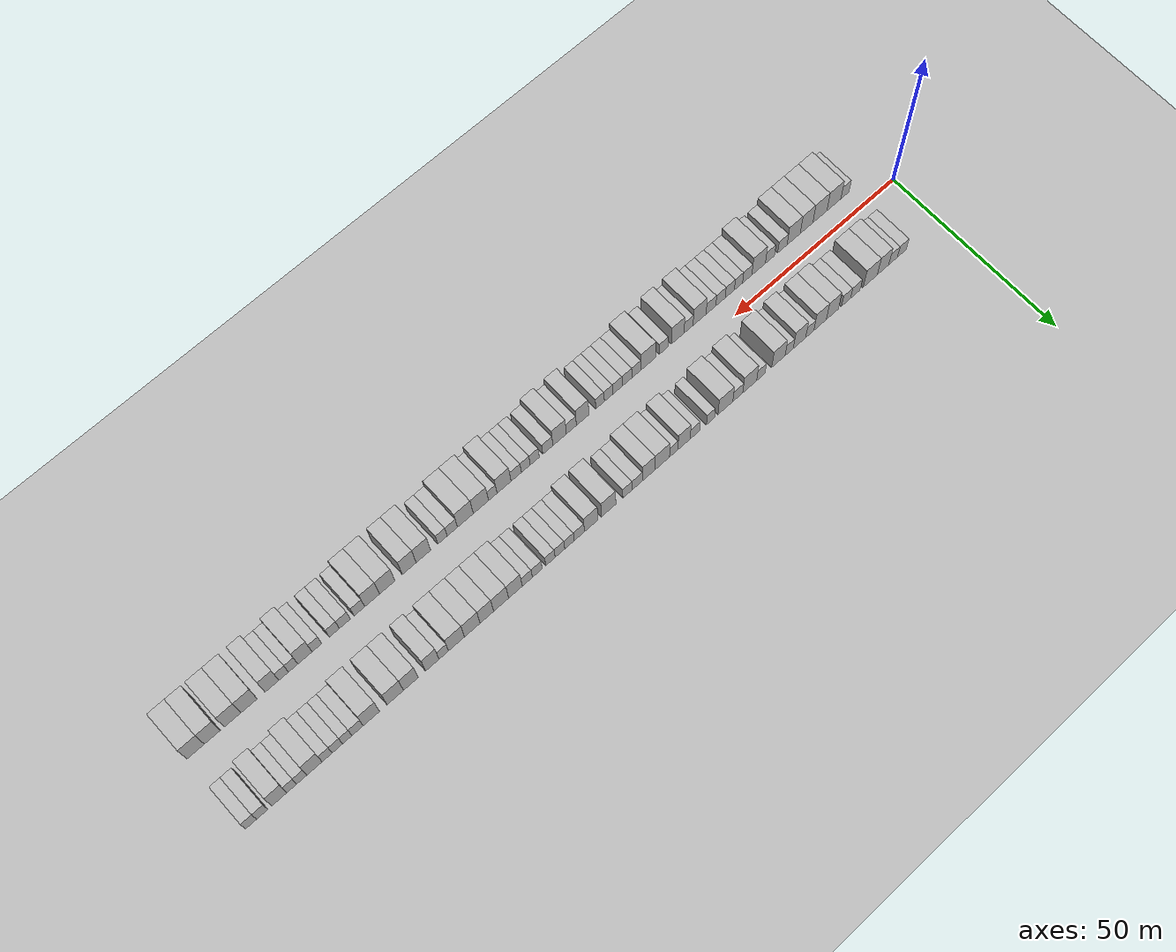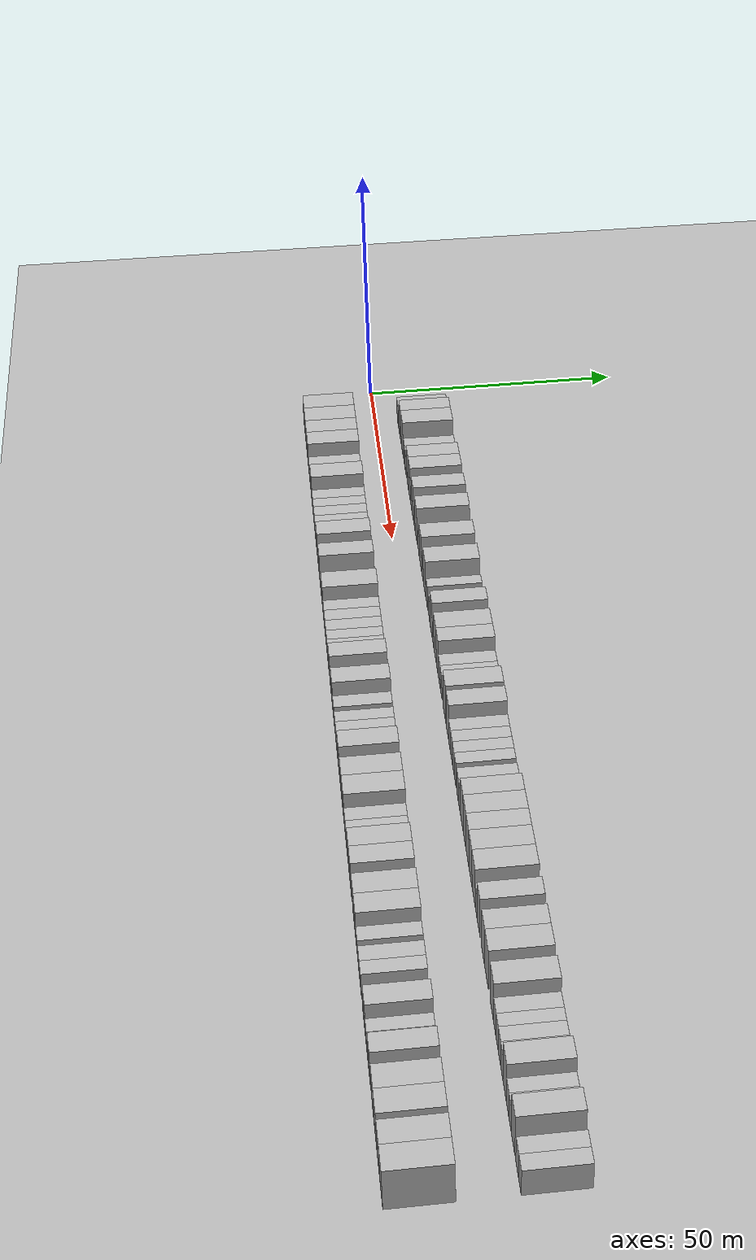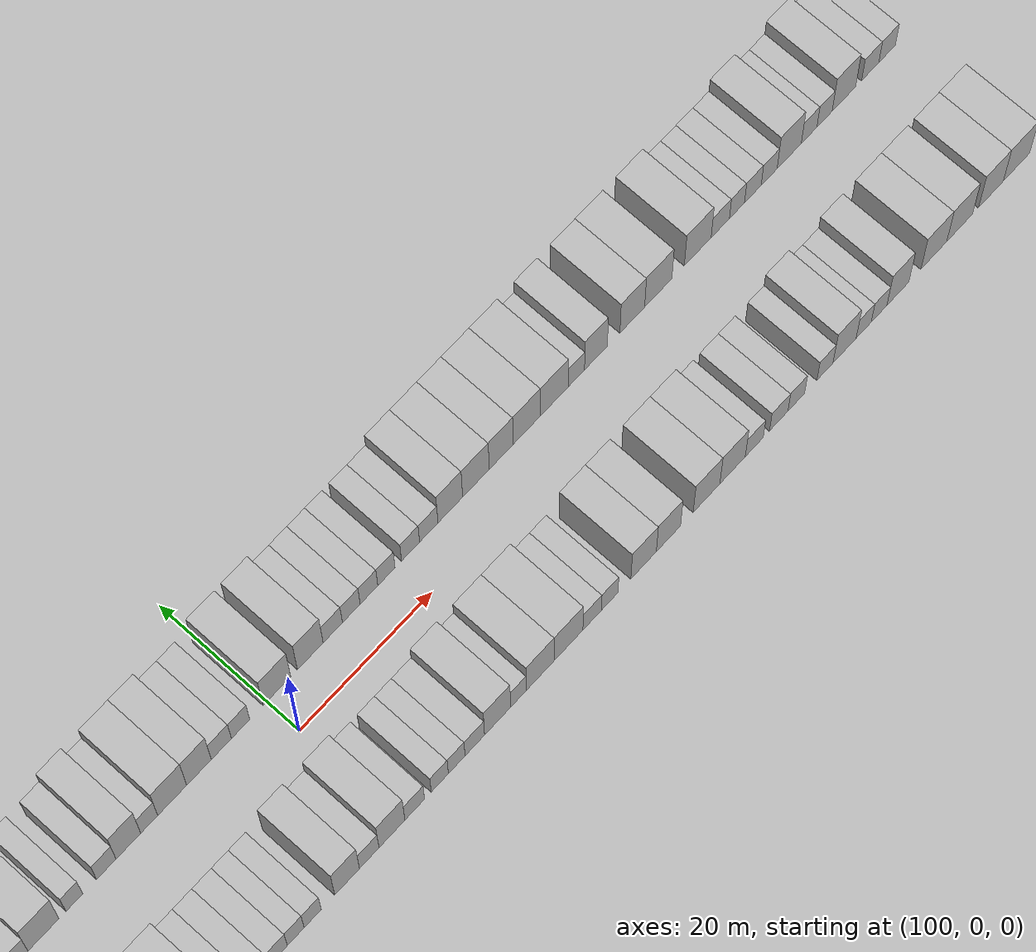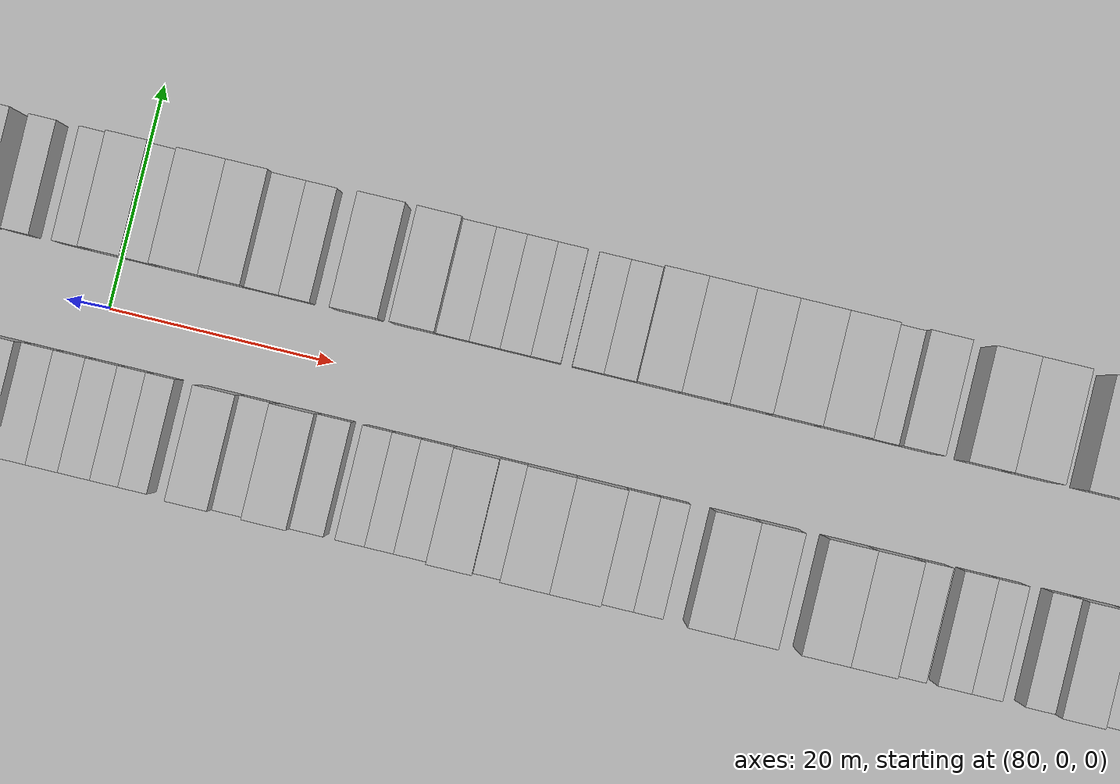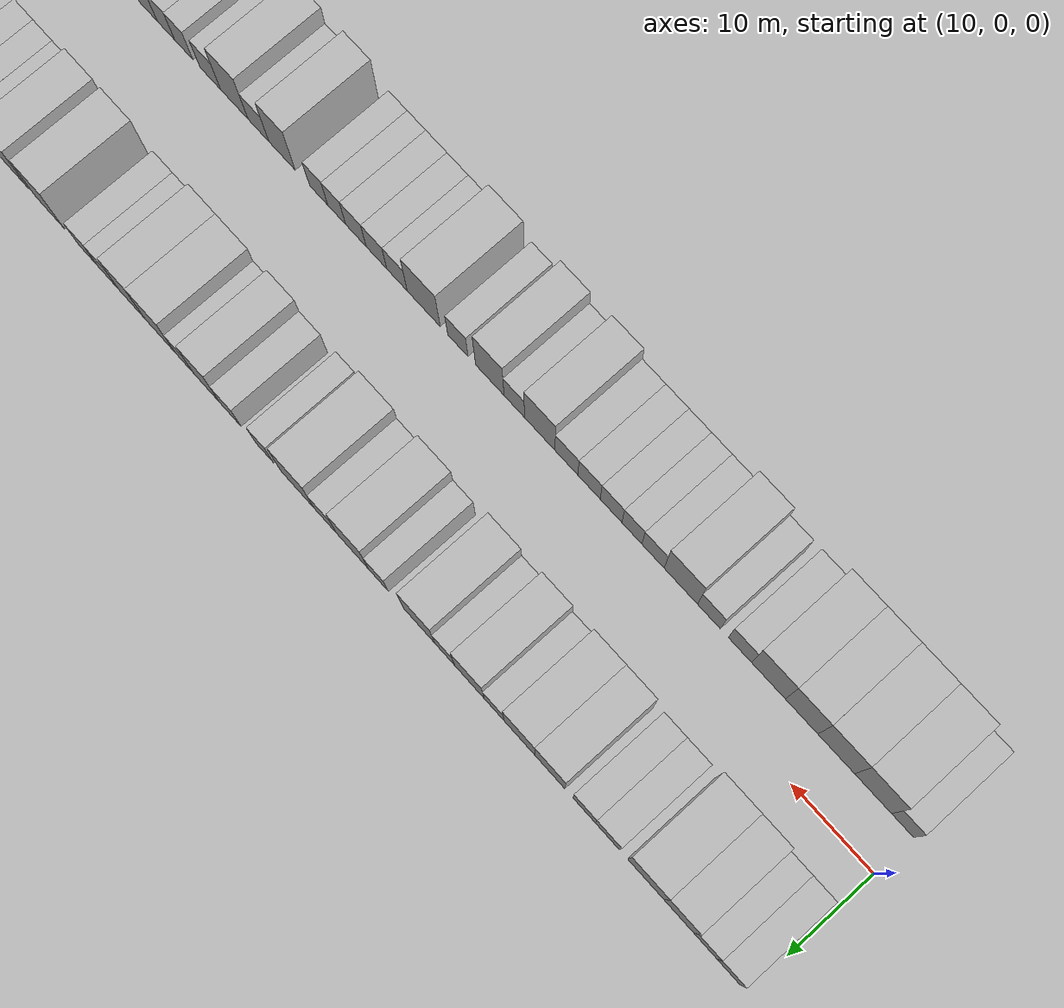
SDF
<?xml version="1.0" encoding="utf-8"?>

<sdf version="1.6">

   <world name="default">

      <gui fullscreen="0">

         <camera name="user_camera">

            <pose>-15 0 4.57585 0 0 0</pose>

            <view_controller>orbit</view_controller>

         </camera>

      </gui>

      <scene>

         <sky>

           <clouds>

             <speed>12</speed>

           </clouds>

         </sky>

         <ambient>0.4 0.4 0.4 1</ambient>

         <background>0.7 0.7 0.7 1</background>

         <shadows>1</shadows>

      </scene>

      <gravity>0 0 -9.8066</gravity>

      <magnetic_field>6e-06 2.3e-05 -4.2e-05</magnetic_field>

      <physics default="0" name="default_physics" type="ode">

         <ode>

            <solver>

               <type>quick</type>

               <iters>10</iters>

               <sor>1.0</sor>

               <use_dynamic_moi_rescaling>0</use_dynamic_moi_rescaling>

            </solver>

            <constraints>

               <cfm>0</cfm>

               <erp>0.2</erp>

               <contact_max_correcting_vel>100</contact_max_correcting_vel>

               <contact_surface_layer>0.001</contact_surface_layer>

            </constraints>

         </ode>

         <max_step_size>0.004</max_step_size>

         <real_time_factor>1</real_time_factor>

         <real_time_update_rate>250</real_time_update_rate>

      </physics>

      <light name="sun" type="directional">

         <cast_shadows>1</cast_shadows>

         <pose>0 0 10 0 0 0</pose>

         <diffuse>0.8 0.8 0.8 1</diffuse>

         <specular>0.2 0.2 0.2 1</specular>

         <attenuation>

            <range>1000</range>

            <constant>0.9</constant>

            <linear>0.01</linear>

            <quadratic>0.001</quadratic>

         </attenuation>

         <direction>-0.5 0.1 -0.9</direction>

      </light>

      <include>

         <name>ground_plane_1</name>

         <uri>model://HANNAS_ground_plane</uri>

         <pose>0 0 0  0 0 0</pose>

      </include>

      <include>

         <name>ground_plane_2</name>

         <uri>model://HANNAS_ground_plane</uri>

         <pose>100 0 0  0 0 0</pose>

      </include>

      <model name="building_1">

         <static>1</static>

         <pose frame="">12.4131 9.5000 0 0.000000 0.000000 1.570796</pose>

         <link name="link">

            <pose frame="">0 0 3.00 0 0 0</pose>

            <collision name="collision">

               <geometry>

                  <box>

                     <size>10.0000 2.8262 6.0000</size>

                  </box>

               </geometry>

               <max_contacts>10</max_contacts>

               <surface>

                  <contact>

                     <ode/>

                  </contact>

                  <bounce/>

                  <friction>

                     <torsional>

                        <ode/>

                     </torsional>

                     <ode/>

                  </friction>

               </surface>

            </collision>

            <visual name="visual">

               <cast_shadows>0</cast_shadows>

               <geometry>

                  <box>

                     <size>10.0000 2.8262 6.0000</size>

                  </box>

               </geometry>

               <material>

                  <script>

                     <uri>model://HANNAS_wall/materials/scripts</uri>

                     <uri>model://HANNAS_wall/materials/textures</uri>

                     <name>vrc/HANNAS_wall</name>

                  </script>

               </material>

            </visual>

            <self_collide>0</self_collide>

            <enable_wind>0</enable_wind>

            <kinematic>0</kinematic>

         </link>

      </model>

      <model name="building_2">

         <static>1</static>

         <pose frame="">15.2293 9.5000 0 0.000000 0.000000 1.570796</pose>

         <link name="link">

            <pose frame="">0 0 3.00 0 0 0</pose>

            <collision name="collision">

               <geometry>

                  <box>

                     <size>10.0000 2.8062 6.0000</size>

                  </box>

               </geometry>

               <max_contacts>10</max_contacts>

               <surface>

                  <contact>

                     <ode/>

                  </contact>

                  <bounce/>

                  <friction>

                     <torsional>

                        <ode/>

                     </torsional>

                     <ode/>

                  </friction>

               </surface>

            </collision>

            <visual name="visual">

               <cast_shadows>0</cast_shadows>

               <geometry>

                  <box>

                     <size>10.0000 2.8062 6.0000</size>

                  </box>

               </geometry>

               <material>

                  <script>

                     <uri>model://HANNAS_wall/materials/scripts</uri>

                     <uri>model://HANNAS_wall/materials/textures</uri>

                     <name>vrc/HANNAS_wall</name>

                  </script>

               </material>

            </visual>

            <self_collide>0</self_collide>

            <enable_wind>0</enable_wind>

            <kinematic>0</kinematic>

         </link>

      </model>

      <model name="building_3">

         <static>1</static>

         <pose frame="">18.4482 9.5000 0 0.000000 0.000000 1.570796</pose>

         <link name="link">

            <pose frame="">0 0 4.50 0 0 0</pose>

            <collision name="collision">

               <geometry>

                  <box>

                     <size>10.0000 3.6314 9.0000</size>

                  </box>

               </geometry>

               <max_contacts>10</max_contacts>

               <surface>

                  <contact>

                     <ode/>

                  </contact>

                  <bounce/>

                  <friction>

                     <torsional>

                        <ode/>

                     </torsional>

                     <ode/>

                  </friction>

               </surface>

            </collision>

            <visual name="visual">

               <cast_shadows>0</cast_shadows>

               <geometry>

                  <box>

                     <size>10.0000 3.6314 9.0000</size>

                  </box>

               </geometry>

               <material>

                  <script>

                     <uri>model://HANNAS_wall/materials/scripts</uri>

                     <uri>model://HANNAS_wall/materials/textures</uri>

                     <name>vrc/HANNAS_wall</name>

                  </script>

               </material>

            </visual>

            <self_collide>0</self_collide>

            <enable_wind>0</enable_wind>

            <kinematic>0</kinematic>

         </link>

      </model>

      <model name="building_4">

         <static>1</static>

         <pose frame="">22.4896 9.5000 0 0.000000 0.000000 1.570796</pose>

         <link name="link">

            <pose frame="">0 0 4.50 0 0 0</pose>

            <collision name="collision">

               <geometry>

                  <box>

                     <size>10.0000 4.4515 9.0000</size>

                  </box>

               </geometry>

               <max_contacts>10</max_contacts>

               <surface>

                  <contact>

                     <ode/>

                  </contact>

                  <bounce/>

                  <friction>

                     <torsional>

                        <ode/>

                     </torsional>

                     <ode/>

                  </friction>

               </surface>

            </collision>

            <visual name="visual">

               <cast_shadows>0</cast_shadows>

               <geometry>

                  <box>

                     <size>10.0000 4.4515 9.0000</size>

                  </box>

               </geometry>

               <material>

                  <script>

                     <uri>model://HANNAS_wall/materials/scripts</uri>

                     <uri>model://HANNAS_wall/materials/textures</uri>

                     <name>vrc/HANNAS_wall</name>

                  </script>

               </material>

            </visual>

            <self_collide>0</self_collide>

            <enable_wind>0</enable_wind>

            <kinematic>0</kinematic>

         </link>

      </model>

      <model name="building_5">

         <static>1</static>

         <pose frame="">27.2118 9.5000 0 0.000000 0.000000 1.570796</pose>

         <link name="link">

            <pose frame="">0 0 3.00 0 0 0</pose>

            <collision name="collision">

               <geometry>

                  <box>

                     <size>10.0000 2.9929 6.0000</size>

                  </box>

               </geometry>

               <max_contacts>10</max_contacts>

               <surface>

                  <contact>

                     <ode/>

                  </contact>

                  <bounce/>

                  <friction>

                     <torsional>

                        <ode/>

                     </torsional>

                     <ode/>

                  </friction>

               </surface>

            </collision>

            <visual name="visual">

               <cast_shadows>0</cast_shadows>

               <geometry>

                  <box>

                     <size>10.0000 2.9929 6.0000</size>

                  </box>

               </geometry>

               <material>

                  <script>

                     <uri>model://HANNAS_wall/materials/scripts</uri>

                     <uri>model://HANNAS_wall/materials/textures</uri>

                     <name>vrc/HANNAS_wall</name>

                  </script>

               </material>

            </visual>

            <self_collide>0</self_collide>

            <enable_wind>0</enable_wind>

            <kinematic>0</kinematic>

         </link>

      </model>

      <model name="building_6">

         <static>1</static>

         <pose frame="">30.1102 9.5000 0 0.000000 0.000000 1.570796</pose>

         <link name="link">

            <pose frame="">0 0 3.00 0 0 0</pose>

            <collision name="collision">

               <geometry>

                  <box>

                     <size>10.0000 2.8040 6.0000</size>

                  </box>

               </geometry>

               <max_contacts>10</max_contacts>

               <surface>

                  <contact>

                     <ode/>

                  </contact>

                  <bounce/>

                  <friction>

                     <torsional>

                        <ode/>

                     </torsional>

                     <ode/>

                  </friction>

               </surface>

            </collision>

            <visual name="visual">

               <cast_shadows>0</cast_shadows>

               <geometry>

                  <box>

                     <size>10.0000 2.8040 6.0000</size>

                  </box>

               </geometry>

               <material>

                  <script>

                     <uri>model://HANNAS_wall/materials/scripts</uri>

                     <uri>model://HANNAS_wall/materials/textures</uri>

                     <name>vrc/HANNAS_wall</name>

                  </script>

               </material>

            </visual>

            <self_collide>0</self_collide>

            <enable_wind>0</enable_wind>

            <kinematic>0</kinematic>

         </link>

      </model>

      <model name="building_7">

         <static>1</static>

         <pose frame="">34.3932 9.5000 0 0.000000 0.000000 1.570796</pose>

         <link name="link">

            <pose frame="">0 0 4.50 0 0 0</pose>

            <collision name="collision">

               <geometry>

                  <box>

                     <size>10.0000 3.7620 9.0000</size>

                  </box>

               </geometry>

               <max_contacts>10</max_contacts>

               <surface>

                  <contact>

                     <ode/>

                  </contact>

                  <bounce/>

                  <friction>

                     <torsional>

                        <ode/>

                     </torsional>

                     <ode/>

                  </friction>

               </surface>

            </collision>

            <visual name="visual">

               <cast_shadows>0</cast_shadows>

               <geometry>

                  <box>

                     <size>10.0000 3.7620 9.0000</size>

                  </box>

               </geometry>

               <material>

                  <script>

                     <uri>model://HANNAS_wall/materials/scripts</uri>

                     <uri>model://HANNAS_wall/materials/textures</uri>

                     <name>vrc/HANNAS_wall</name>

                  </script>

               </material>

            </visual>

            <self_collide>0</self_collide>

            <enable_wind>0</enable_wind>

            <kinematic>0</kinematic>

         </link>

      </model>

      <model name="building_8">

         <static>1</static>

         <pose frame="">38.2200 9.5000 0 0.000000 0.000000 1.570796</pose>

         <link name="link">

            <pose frame="">0 0 4.50 0 0 0</pose>

            <collision name="collision">

               <geometry>

                  <box>

                     <size>10.0000 3.8916 9.0000</size>

                  </box>

               </geometry>

               <max_contacts>10</max_contacts>

               <surface>

                  <contact>

                     <ode/>

                  </contact>

                  <bounce/>

                  <friction>

                     <torsional>

                        <ode/>

                     </torsional>

                     <ode/>

                  </friction>

               </surface>

            </collision>

            <visual name="visual">

               <cast_shadows>0</cast_shadows>

               <geometry>

                  <box>

                     <size>10.0000 3.8916 9.0000</size>

                  </box>

               </geometry>

               <material>

                  <script>

                     <uri>model://HANNAS_wall/materials/scripts</uri>

                     <uri>model://HANNAS_wall/materials/textures</uri>

                     <name>vrc/HANNAS_wall</name>

                  </script>

               </material>

            </visual>

            <self_collide>0</self_collide>

            <enable_wind>0</enable_wind>

            <kinematic>0</kinematic>

         </link>

      </model>

      <model name="building_9">

         <static>1</static>

         <pose frame="">41.4322 9.5000 0 0.000000 0.000000 1.570796</pose>

         <link name="link">

            <pose frame="">0 0 3.00 0 0 0</pose>

            <collision name="collision">

               <geometry>

                  <box>

                     <size>10.0000 2.5330 6.0000</size>

                  </box>

               </geometry>

               <max_contacts>10</max_contacts>

               <surface>

                  <contact>

                     <ode/>

                  </contact>

                  <bounce/>

                  <friction>

                     <torsional>

                        <ode/>

                     </torsional>

                     <ode/>

                  </friction>

               </surface>

            </collision>

            <visual name="visual">

               <cast_shadows>0</cast_shadows>

               <geometry>

                  <box>

                     <size>10.0000 2.5330 6.0000</size>

                  </box>

               </geometry>

               <material>

                  <script>

                     <uri>model://HANNAS_wall/materials/scripts</uri>

                     <uri>model://HANNAS_wall/materials/textures</uri>

                     <name>vrc/HANNAS_wall</name>

                  </script>

               </material>

            </visual>

            <self_collide>0</self_collide>

            <enable_wind>0</enable_wind>

            <kinematic>0</kinematic>

         </link>

      </model>

      <model name="building_10">

         <static>1</static>

         <pose frame="">44.6003 9.5000 0 0.000000 0.000000 1.570796</pose>

         <link name="link">

            <pose frame="">0 0 4.50 0 0 0</pose>

            <collision name="collision">

               <geometry>

                  <box>

                     <size>10.0000 3.8032 9.0000</size>

                  </box>

               </geometry>

               <max_contacts>10</max_contacts>

               <surface>

                  <contact>

                     <ode/>

                  </contact>

                  <bounce/>

                  <friction>

                     <torsional>

                        <ode/>

                     </torsional>

                     <ode/>

                  </friction>

               </surface>

            </collision>

            <visual name="visual">

               <cast_shadows>0</cast_shadows>

               <geometry>

                  <box>

                     <size>10.0000 3.8032 9.0000</size>

                  </box>

               </geometry>

               <material>

                  <script>

                     <uri>model://HANNAS_wall/materials/scripts</uri>

                     <uri>model://HANNAS_wall/materials/textures</uri>

                     <name>vrc/HANNAS_wall</name>

                  </script>

               </material>

            </visual>

            <self_collide>0</self_collide>

            <enable_wind>0</enable_wind>

            <kinematic>0</kinematic>

         </link>

      </model>

      <model name="building_11">

         <static>1</static>

         <pose frame="">47.7659 9.5000 0 0.000000 0.000000 1.570796</pose>

         <link name="link">

            <pose frame="">0 0 3.00 0 0 0</pose>

            <collision name="collision">

               <geometry>

                  <box>

                     <size>10.0000 2.5279 6.0000</size>

                  </box>

               </geometry>

               <max_contacts>10</max_contacts>

               <surface>

                  <contact>

                     <ode/>

                  </contact>

                  <bounce/>

                  <friction>

                     <torsional>

                        <ode/>

                     </torsional>

                     <ode/>

                  </friction>

               </surface>

            </collision>

            <visual name="visual">

               <cast_shadows>0</cast_shadows>

               <geometry>

                  <box>

                     <size>10.0000 2.5279 6.0000</size>

                  </box>

               </geometry>

               <material>

                  <script>

                     <uri>model://HANNAS_wall/materials/scripts</uri>

                     <uri>model://HANNAS_wall/materials/textures</uri>

                     <name>vrc/HANNAS_wall</name>

                  </script>

               </material>

            </visual>

            <self_collide>0</self_collide>

            <enable_wind>0</enable_wind>

            <kinematic>0</kinematic>

         </link>

      </model>

      <model name="building_12">

         <static>1</static>

         <pose frame="">51.0742 9.5000 0 0.000000 0.000000 1.570796</pose>

         <link name="link">

            <pose frame="">0 0 4.50 0 0 0</pose>

            <collision name="collision">

               <geometry>

                  <box>

                     <size>10.0000 4.0886 9.0000</size>

                  </box>

               </geometry>

               <max_contacts>10</max_contacts>

               <surface>

                  <contact>

                     <ode/>

                  </contact>

                  <bounce/>

                  <friction>

                     <torsional>

                        <ode/>

                     </torsional>

                     <ode/>

                  </friction>

               </surface>

            </collision>

            <visual name="visual">

               <cast_shadows>0</cast_shadows>

               <geometry>

                  <box>

                     <size>10.0000 4.0886 9.0000</size>

                  </box>

               </geometry>

               <material>

                  <script>

                     <uri>model://HANNAS_wall/materials/scripts</uri>

                     <uri>model://HANNAS_wall/materials/textures</uri>

                     <name>vrc/HANNAS_wall</name>

                  </script>

               </material>

            </visual>

            <self_collide>0</self_collide>

            <enable_wind>0</enable_wind>

            <kinematic>0</kinematic>

         </link>

      </model>

      <model name="building_13">

         <static>1</static>

         <pose frame="">56.4108 9.5000 0 0.000000 0.000000 1.570796</pose>

         <link name="link">

            <pose frame="">0 0 3.00 0 0 0</pose>

            <collision name="collision">

               <geometry>

                  <box>

                     <size>10.0000 2.5846 6.0000</size>

                  </box>

               </geometry>

               <max_contacts>10</max_contacts>

               <surface>

                  <contact>

                     <ode/>

                  </contact>

                  <bounce/>

                  <friction>

                     <torsional>

                        <ode/>

                     </torsional>

                     <ode/>

                  </friction>

               </surface>

            </collision>

            <visual name="visual">

               <cast_shadows>0</cast_shadows>

               <geometry>

                  <box>

                     <size>10.0000 2.5846 6.0000</size>

                  </box>

               </geometry>

               <material>

                  <script>

                     <uri>model://HANNAS_wall/materials/scripts</uri>

                     <uri>model://HANNAS_wall/materials/textures</uri>

                     <name>vrc/HANNAS_wall</name>

                  </script>

               </material>

            </visual>

            <self_collide>0</self_collide>

            <enable_wind>0</enable_wind>

            <kinematic>0</kinematic>

         </link>

      </model>

      <model name="building_14">

         <static>1</static>

         <pose frame="">59.8139 9.5000 0 0.000000 0.000000 1.570796</pose>

         <link name="link">

            <pose frame="">0 0 4.50 0 0 0</pose>

            <collision name="collision">

               <geometry>

                  <box>

                     <size>10.0000 4.2217 9.0000</size>

                  </box>

               </geometry>

               <max_contacts>10</max_contacts>

               <surface>

                  <contact>

                     <ode/>

                  </contact>

                  <bounce/>

                  <friction>

                     <torsional>

                        <ode/>

                     </torsional>

                     <ode/>

                  </friction>

               </surface>

            </collision>

            <visual name="visual">

               <cast_shadows>0</cast_shadows>

               <geometry>

                  <box>

                     <size>10.0000 4.2217 9.0000</size>

                  </box>

               </geometry>

               <material>

                  <script>

                     <uri>model://HANNAS_wall/materials/scripts</uri>

                     <uri>model://HANNAS_wall/materials/textures</uri>

                     <name>vrc/HANNAS_wall</name>

                  </script>

               </material>

            </visual>

            <self_collide>0</self_collide>

            <enable_wind>0</enable_wind>

            <kinematic>0</kinematic>

         </link>

      </model>

      <model name="building_15">

         <static>1</static>

         <pose frame="">63.4169 9.5000 0 0.000000 0.000000 1.570796</pose>

         <link name="link">

            <pose frame="">0 0 3.00 0 0 0</pose>

            <collision name="collision">

               <geometry>

                  <box>

                     <size>10.0000 2.9843 6.0000</size>

                  </box>

               </geometry>

               <max_contacts>10</max_contacts>

               <surface>

                  <contact>

                     <ode/>

                  </contact>

                  <bounce/>

                  <friction>

                     <torsional>

                        <ode/>

                     </torsional>

                     <ode/>

                  </friction>

               </surface>

            </collision>

            <visual name="visual">

               <cast_shadows>0</cast_shadows>

               <geometry>

                  <box>

                     <size>10.0000 2.9843 6.0000</size>

                  </box>

               </geometry>

               <material>

                  <script>

                     <uri>model://HANNAS_wall/materials/scripts</uri>

                     <uri>model://HANNAS_wall/materials/textures</uri>

                     <name>vrc/HANNAS_wall</name>

                  </script>

               </material>

            </visual>

            <self_collide>0</self_collide>

            <enable_wind>0</enable_wind>

            <kinematic>0</kinematic>

         </link>

      </model>

      <model name="building_16">

         <static>1</static>

         <pose frame="">67.1395 9.5000 0 0.000000 0.000000 1.570796</pose>

         <link name="link">

            <pose frame="">0 0 4.50 0 0 0</pose>

            <collision name="collision">

               <geometry>

                  <box>

                     <size>10.0000 4.4609 9.0000</size>

                  </box>

               </geometry>

               <max_contacts>10</max_contacts>

               <surface>

                  <contact>

                     <ode/>

                  </contact>

                  <bounce/>

                  <friction>

                     <torsional>

                        <ode/>

                     </torsional>

                     <ode/>

                  </friction>

               </surface>

            </collision>

            <visual name="visual">

               <cast_shadows>0</cast_shadows>

               <geometry>

                  <box>

                     <size>10.0000 4.4609 9.0000</size>

                  </box>

               </geometry>

               <material>

                  <script>

                     <uri>model://HANNAS_wall/materials/scripts</uri>

                     <uri>model://HANNAS_wall/materials/textures</uri>

                     <name>vrc/HANNAS_wall</name>

                  </script>

               </material>

            </visual>

            <self_collide>0</self_collide>

            <enable_wind>0</enable_wind>

            <kinematic>0</kinematic>

         </link>

      </model>

      <model name="building_17">

         <static>1</static>

         <pose frame="">71.5821 9.5000 0 0.000000 0.000000 1.570796</pose>

         <link name="link">

            <pose frame="">0 0 3.00 0 0 0</pose>

            <collision name="collision">

               <geometry>

                  <box>

                     <size>10.0000 2.4243 6.0000</size>

                  </box>

               </geometry>

               <max_contacts>10</max_contacts>

               <surface>

                  <contact>

                     <ode/>

                  </contact>

                  <bounce/>

                  <friction>

                     <torsional>

                        <ode/>

                     </torsional>

                     <ode/>

                  </friction>

               </surface>

            </collision>

            <visual name="visual">

               <cast_shadows>0</cast_shadows>

               <geometry>

                  <box>

                     <size>10.0000 2.4243 6.0000</size>

                  </box>

               </geometry>

               <material>

                  <script>

                     <uri>model://HANNAS_wall/materials/scripts</uri>

                     <uri>model://HANNAS_wall/materials/textures</uri>

                     <name>vrc/HANNAS_wall</name>

                  </script>

               </material>

            </visual>

            <self_collide>0</self_collide>

            <enable_wind>0</enable_wind>

            <kinematic>0</kinematic>

         </link>

      </model>

      <model name="building_18">

         <static>1</static>

         <pose frame="">76.2130 9.5000 0 0.000000 0.000000 1.570796</pose>

         <link name="link">

            <pose frame="">0 0 3.00 0 0 0</pose>

            <collision name="collision">

               <geometry>

                  <box>

                     <size>10.0000 2.8375 6.0000</size>

                  </box>

               </geometry>

               <max_contacts>10</max_contacts>

               <surface>

                  <contact>

                     <ode/>

                  </contact>

                  <bounce/>

                  <friction>

                     <torsional>

                        <ode/>

                     </torsional>

                     <ode/>

                  </friction>

               </surface>

            </collision>

            <visual name="visual">

               <cast_shadows>0</cast_shadows>

               <geometry>

                  <box>

                     <size>10.0000 2.8375 6.0000</size>

                  </box>

               </geometry>

               <material>

                  <script>

                     <uri>model://HANNAS_wall/materials/scripts</uri>

                     <uri>model://HANNAS_wall/materials/textures</uri>

                     <name>vrc/HANNAS_wall</name>

                  </script>

               </material>

            </visual>

            <self_collide>0</self_collide>

            <enable_wind>0</enable_wind>

            <kinematic>0</kinematic>

         </link>

      </model>

      <model name="building_19">

         <static>1</static>

         <pose frame="">79.4336 9.5000 0 0.000000 0.000000 1.570796</pose>

         <link name="link">

            <pose frame="">0 0 4.50 0 0 0</pose>

            <collision name="collision">

               <geometry>

                  <box>

                     <size>10.0000 3.6037 9.0000</size>

                  </box>

               </geometry>

               <max_contacts>10</max_contacts>

               <surface>

                  <contact>

                     <ode/>

                  </contact>

                  <bounce/>

                  <friction>

                     <torsional>

                        <ode/>

                     </torsional>

                     <ode/>

                  </friction>

               </surface>

            </collision>

            <visual name="visual">

               <cast_shadows>0</cast_shadows>

               <geometry>

                  <box>

                     <size>10.0000 3.6037 9.0000</size>

                  </box>

               </geometry>

               <material>

                  <script>

                     <uri>model://HANNAS_wall/materials/scripts</uri>

                     <uri>model://HANNAS_wall/materials/textures</uri>

                     <name>vrc/HANNAS_wall</name>

                  </script>

               </material>

            </visual>

            <self_collide>0</self_collide>

            <enable_wind>0</enable_wind>

            <kinematic>0</kinematic>

         </link>

      </model>

      <model name="building_20">

         <static>1</static>

         <pose frame="">82.4817 9.5000 0 0.000000 0.000000 1.570796</pose>

         <link name="link">

            <pose frame="">0 0 3.00 0 0 0</pose>

            <collision name="collision">

               <geometry>

                  <box>

                     <size>10.0000 2.4925 6.0000</size>

                  </box>

               </geometry>

               <max_contacts>10</max_contacts>

               <surface>

                  <contact>

                     <ode/>

                  </contact>

                  <bounce/>

                  <friction>

                     <torsional>

                        <ode/>

                     </torsional>

                     <ode/>

                  </friction>

               </surface>

            </collision>

            <visual name="visual">

               <cast_shadows>0</cast_shadows>

               <geometry>

                  <box>

                     <size>10.0000 2.4925 6.0000</size>

                  </box>

               </geometry>

               <material>

                  <script>

                     <uri>model://HANNAS_wall/materials/scripts</uri>

                     <uri>model://HANNAS_wall/materials/textures</uri>

                     <name>vrc/HANNAS_wall</name>

                  </script>

               </material>

            </visual>

            <self_collide>0</self_collide>

            <enable_wind>0</enable_wind>

            <kinematic>0</kinematic>

         </link>

      </model>

      <model name="building_21">

         <static>1</static>

         <pose frame="">85.8562 9.5000 0 0.000000 0.000000 1.570796</pose>

         <link name="link">

            <pose frame="">0 0 4.50 0 0 0</pose>

            <collision name="collision">

               <geometry>

                  <box>

                     <size>10.0000 4.2565 9.0000</size>

                  </box>

               </geometry>

               <max_contacts>10</max_contacts>

               <surface>

                  <contact>

                     <ode/>

                  </contact>

                  <bounce/>

                  <friction>

                     <torsional>

                        <ode/>

                     </torsional>

                     <ode/>

                  </friction>

               </surface>

            </collision>

            <visual name="visual">

               <cast_shadows>0</cast_shadows>

               <geometry>

                  <box>

                     <size>10.0000 4.2565 9.0000</size>

                  </box>

               </geometry>

               <material>

                  <script>

                     <uri>model://HANNAS_wall/materials/scripts</uri>

                     <uri>model://HANNAS_wall/materials/textures</uri>

                     <name>vrc/HANNAS_wall</name>

                  </script>

               </material>

            </visual>

            <self_collide>0</self_collide>

            <enable_wind>0</enable_wind>

            <kinematic>0</kinematic>

         </link>

      </model>

      <model name="building_22">

         <static>1</static>

         <pose frame="">89.8014 9.5000 0 0.000000 0.000000 1.570796</pose>

         <link name="link">

            <pose frame="">0 0 4.50 0 0 0</pose>

            <collision name="collision">

               <geometry>

                  <box>

                     <size>10.0000 3.6340 9.0000</size>

                  </box>

               </geometry>

               <max_contacts>10</max_contacts>

               <surface>

                  <contact>

                     <ode/>

                  </contact>

                  <bounce/>

                  <friction>

                     <torsional>

                        <ode/>

                     </torsional>

                     <ode/>

                  </friction>

               </surface>

            </collision>

            <visual name="visual">

               <cast_shadows>0</cast_shadows>

               <geometry>

                  <box>

                     <size>10.0000 3.6340 9.0000</size>

                  </box>

               </geometry>

               <material>

                  <script>

                     <uri>model://HANNAS_wall/materials/scripts</uri>

                     <uri>model://HANNAS_wall/materials/textures</uri>

                     <name>vrc/HANNAS_wall</name>

                  </script>

               </material>

            </visual>

            <self_collide>0</self_collide>

            <enable_wind>0</enable_wind>

            <kinematic>0</kinematic>

         </link>

      </model>

      <model name="building_23">

         <static>1</static>

         <pose frame="">93.1143 9.5000 0 0.000000 0.000000 1.570796</pose>

         <link name="link">

            <pose frame="">0 0 3.00 0 0 0</pose>

            <collision name="collision">

               <geometry>

                  <box>

                     <size>10.0000 2.9918 6.0000</size>

                  </box>

               </geometry>

               <max_contacts>10</max_contacts>

               <surface>

                  <contact>

                     <ode/>

                  </contact>

                  <bounce/>

                  <friction>

                     <torsional>

                        <ode/>

                     </torsional>

                     <ode/>

                  </friction>

               </surface>

            </collision>

            <visual name="visual">

               <cast_shadows>0</cast_shadows>

               <geometry>

                  <box>

                     <size>10.0000 2.9918 6.0000</size>

                  </box>

               </geometry>

               <material>

                  <script>

                     <uri>model://HANNAS_wall/materials/scripts</uri>

                     <uri>model://HANNAS_wall/materials/textures</uri>

                     <name>vrc/HANNAS_wall</name>

                  </script>

               </material>

            </visual>

            <self_collide>0</self_collide>

            <enable_wind>0</enable_wind>

            <kinematic>0</kinematic>

         </link>

      </model>

      <model name="building_24">

         <static>1</static>

         <pose frame="">95.9690 9.5000 0 0.000000 0.000000 1.570796</pose>

         <link name="link">

            <pose frame="">0 0 3.00 0 0 0</pose>

            <collision name="collision">

               <geometry>

                  <box>

                     <size>10.0000 2.7175 6.0000</size>

                  </box>

               </geometry>

               <max_contacts>10</max_contacts>

               <surface>

                  <contact>

                     <ode/>

                  </contact>

                  <bounce/>

                  <friction>

                     <torsional>

                        <ode/>

                     </torsional>

                     <ode/>

                  </friction>

               </surface>

            </collision>

            <visual name="visual">

               <cast_shadows>0</cast_shadows>

               <geometry>

                  <box>

                     <size>10.0000 2.7175 6.0000</size>

                  </box>

               </geometry>

               <material>

                  <script>

                     <uri>model://HANNAS_wall/materials/scripts</uri>

                     <uri>model://HANNAS_wall/materials/textures</uri>

                     <name>vrc/HANNAS_wall</name>

                  </script>

               </material>

            </visual>

            <self_collide>0</self_collide>

            <enable_wind>0</enable_wind>

            <kinematic>0</kinematic>

         </link>

      </model>

      <model name="building_25">

         <static>1</static>

         <pose frame="">101.3992 9.5000 0 0.000000 0.000000 1.570796</pose>

         <link name="link">

            <pose frame="">0 0 4.50 0 0 0</pose>

            <collision name="collision">

               <geometry>

                  <box>

                     <size>10.0000 4.1428 9.0000</size>

                  </box>

               </geometry>

               <max_contacts>10</max_contacts>

               <surface>

                  <contact>

                     <ode/>

                  </contact>

                  <bounce/>

                  <friction>

                     <torsional>

                        <ode/>

                     </torsional>

                     <ode/>

                  </friction>

               </surface>

            </collision>

            <visual name="visual">

               <cast_shadows>0</cast_shadows>

               <geometry>

                  <box>

                     <size>10.0000 4.1428 9.0000</size>

                  </box>

               </geometry>

               <material>

                  <script>

                     <uri>model://HANNAS_wall/materials/scripts</uri>

                     <uri>model://HANNAS_wall/materials/textures</uri>

                     <name>vrc/HANNAS_wall</name>

                  </script>

               </material>

            </visual>

            <self_collide>0</self_collide>

            <enable_wind>0</enable_wind>

            <kinematic>0</kinematic>

         </link>

      </model>

      <model name="building_26">

         <static>1</static>

         <pose frame="">106.4077 9.5000 0 0.000000 0.000000 1.570796</pose>

         <link name="link">

            <pose frame="">0 0 4.50 0 0 0</pose>

            <collision name="collision">

               <geometry>

                  <box>

                     <size>10.0000 3.8743 9.0000</size>

                  </box>

               </geometry>

               <max_contacts>10</max_contacts>

               <surface>

                  <contact>

                     <ode/>

                  </contact>

                  <bounce/>

                  <friction>

                     <torsional>

                        <ode/>

                     </torsional>

                     <ode/>

                  </friction>

               </surface>

            </collision>

            <visual name="visual">

               <cast_shadows>0</cast_shadows>

               <geometry>

                  <box>

                     <size>10.0000 3.8743 9.0000</size>

                  </box>

               </geometry>

               <material>

                  <script>

                     <uri>model://HANNAS_wall/materials/scripts</uri>

                     <uri>model://HANNAS_wall/materials/textures</uri>

                     <name>vrc/HANNAS_wall</name>

                  </script>

               </material>

            </visual>

            <self_collide>0</self_collide>

            <enable_wind>0</enable_wind>

            <kinematic>0</kinematic>

         </link>

      </model>

      <model name="building_27">

         <static>1</static>

         <pose frame="">109.8046 9.5000 0 0.000000 0.000000 1.570796</pose>

         <link name="link">

            <pose frame="">0 0 3.00 0 0 0</pose>

            <collision name="collision">

               <geometry>

                  <box>

                     <size>10.0000 2.9195 6.0000</size>

                  </box>

               </geometry>

               <max_contacts>10</max_contacts>

               <surface>

                  <contact>

                     <ode/>

                  </contact>

                  <bounce/>

                  <friction>

                     <torsional>

                        <ode/>

                     </torsional>

                     <ode/>

                  </friction>

               </surface>

            </collision>

            <visual name="visual">

               <cast_shadows>0</cast_shadows>

               <geometry>

                  <box>

                     <size>10.0000 2.9195 6.0000</size>

                  </box>

               </geometry>

               <material>

                  <script>

                     <uri>model://HANNAS_wall/materials/scripts</uri>

                     <uri>model://HANNAS_wall/materials/textures</uri>

                     <name>vrc/HANNAS_wall</name>

                  </script>

               </material>

            </visual>

            <self_collide>0</self_collide>

            <enable_wind>0</enable_wind>

            <kinematic>0</kinematic>

         </link>

      </model>

      <model name="building_28">

         <static>1</static>

         <pose frame="">112.6101 9.5000 0 0.000000 0.000000 1.570796</pose>

         <link name="link">

            <pose frame="">0 0 3.00 0 0 0</pose>

            <collision name="collision">

               <geometry>

                  <box>

                     <size>10.0000 2.6914 6.0000</size>

                  </box>

               </geometry>

               <max_contacts>10</max_contacts>

               <surface>

                  <contact>

                     <ode/>

                  </contact>

                  <bounce/>

                  <friction>

                     <torsional>

                        <ode/>

                     </torsional>

                     <ode/>

                  </friction>

               </surface>

            </collision>

            <visual name="visual">

               <cast_shadows>0</cast_shadows>

               <geometry>

                  <box>

                     <size>10.0000 2.6914 6.0000</size>

                  </box>

               </geometry>

               <material>

                  <script>

                     <uri>model://HANNAS_wall/materials/scripts</uri>

                     <uri>model://HANNAS_wall/materials/textures</uri>

                     <name>vrc/HANNAS_wall</name>

                  </script>

               </material>

            </visual>

            <self_collide>0</self_collide>

            <enable_wind>0</enable_wind>

            <kinematic>0</kinematic>

         </link>

      </model>

      <model name="building_29">

         <static>1</static>

         <pose frame="">115.3013 9.5000 0 0.000000 0.000000 1.570796</pose>

         <link name="link">

            <pose frame="">0 0 3.00 0 0 0</pose>

            <collision name="collision">

               <geometry>

                  <box>

                     <size>10.0000 2.6911 6.0000</size>

                  </box>

               </geometry>

               <max_contacts>10</max_contacts>

               <surface>

                  <contact>

                     <ode/>

                  </contact>

                  <bounce/>

                  <friction>

                     <torsional>

                        <ode/>

                     </torsional>

                     <ode/>

                  </friction>

               </surface>

            </collision>

            <visual name="visual">

               <cast_shadows>0</cast_shadows>

               <geometry>

                  <box>

                     <size>10.0000 2.6911 6.0000</size>

                  </box>

               </geometry>

               <material>

                  <script>

                     <uri>model://HANNAS_wall/materials/scripts</uri>

                     <uri>model://HANNAS_wall/materials/textures</uri>

                     <name>vrc/HANNAS_wall</name>

                  </script>

               </material>

            </visual>

            <self_collide>0</self_collide>

            <enable_wind>0</enable_wind>

            <kinematic>0</kinematic>

         </link>

      </model>

      <model name="building_30">

         <static>1</static>

         <pose frame="">117.9586 9.5000 0 0.000000 0.000000 1.570796</pose>

         <link name="link">

            <pose frame="">0 0 3.00 0 0 0</pose>

            <collision name="collision">

               <geometry>

                  <box>

                     <size>10.0000 2.6236 6.0000</size>

                  </box>

               </geometry>

               <max_contacts>10</max_contacts>

               <surface>

                  <contact>

                     <ode/>

                  </contact>

                  <bounce/>

                  <friction>

                     <torsional>

                        <ode/>

                     </torsional>

                     <ode/>

                  </friction>

               </surface>

            </collision>

            <visual name="visual">

               <cast_shadows>0</cast_shadows>

               <geometry>

                  <box>

                     <size>10.0000 2.6236 6.0000</size>

                  </box>

               </geometry>

               <material>

                  <script>

                     <uri>model://HANNAS_wall/materials/scripts</uri>

                     <uri>model://HANNAS_wall/materials/textures</uri>

                     <name>vrc/HANNAS_wall</name>

                  </script>

               </material>

            </visual>

            <self_collide>0</self_collide>

            <enable_wind>0</enable_wind>

            <kinematic>0</kinematic>

         </link>

      </model>

      <model name="building_31">

         <static>1</static>

         <pose frame="">121.6517 9.5000 0 0.000000 0.000000 1.570796</pose>

         <link name="link">

            <pose frame="">0 0 3.00 0 0 0</pose>

            <collision name="collision">

               <geometry>

                  <box>

                     <size>10.0000 2.7625 6.0000</size>

                  </box>

               </geometry>

               <max_contacts>10</max_contacts>

               <surface>

                  <contact>

                     <ode/>

                  </contact>

                  <bounce/>

                  <friction>

                     <torsional>

                        <ode/>

                     </torsional>

                     <ode/>

                  </friction>

               </surface>

            </collision>

            <visual name="visual">

               <cast_shadows>0</cast_shadows>

               <geometry>

                  <box>

                     <size>10.0000 2.7625 6.0000</size>

                  </box>

               </geometry>

               <material>

                  <script>

                     <uri>model://HANNAS_wall/materials/scripts</uri>

                     <uri>model://HANNAS_wall/materials/textures</uri>

                     <name>vrc/HANNAS_wall</name>

                  </script>

               </material>

            </visual>

            <self_collide>0</self_collide>

            <enable_wind>0</enable_wind>

            <kinematic>0</kinematic>

         </link>

      </model>

      <model name="building_32">

         <static>1</static>

         <pose frame="">124.4474 9.5000 0 0.000000 0.000000 1.570796</pose>

         <link name="link">

            <pose frame="">0 0 3.00 0 0 0</pose>

            <collision name="collision">

               <geometry>

                  <box>

                     <size>10.0000 2.8290 6.0000</size>

                  </box>

               </geometry>

               <max_contacts>10</max_contacts>

               <surface>

                  <contact>

                     <ode/>

                  </contact>

                  <bounce/>

                  <friction>

                     <torsional>

                        <ode/>

                     </torsional>

                     <ode/>

                  </friction>

               </surface>

            </collision>

            <visual name="visual">

               <cast_shadows>0</cast_shadows>

               <geometry>

                  <box>

                     <size>10.0000 2.8290 6.0000</size>

                  </box>

               </geometry>

               <material>

                  <script>

                     <uri>model://HANNAS_wall/materials/scripts</uri>

                     <uri>model://HANNAS_wall/materials/textures</uri>

                     <name>vrc/HANNAS_wall</name>

                  </script>

               </material>

            </visual>

            <self_collide>0</self_collide>

            <enable_wind>0</enable_wind>

            <kinematic>0</kinematic>

         </link>

      </model>

      <model name="building_33">

         <static>1</static>

         <pose frame="">127.7684 9.5000 0 0.000000 0.000000 1.570796</pose>

         <link name="link">

            <pose frame="">0 0 4.50 0 0 0</pose>

            <collision name="collision">

               <geometry>

                  <box>

                     <size>10.0000 3.8130 9.0000</size>

                  </box>

               </geometry>

               <max_contacts>10</max_contacts>

               <surface>

                  <contact>

                     <ode/>

                  </contact>

                  <bounce/>

                  <friction>

                     <torsional>

                        <ode/>

                     </torsional>

                     <ode/>

                  </friction>

               </surface>

            </collision>

            <visual name="visual">

               <cast_shadows>0</cast_shadows>

               <geometry>

                  <box>

                     <size>10.0000 3.8130 9.0000</size>

                  </box>

               </geometry>

               <material>

                  <script>

                     <uri>model://HANNAS_wall/materials/scripts</uri>

                     <uri>model://HANNAS_wall/materials/textures</uri>

                     <name>vrc/HANNAS_wall</name>

                  </script>

               </material>

            </visual>

            <self_collide>0</self_collide>

            <enable_wind>0</enable_wind>

            <kinematic>0</kinematic>

         </link>

      </model>

      <model name="building_34">

         <static>1</static>

         <pose frame="">131.7432 9.5000 0 0.000000 0.000000 1.570796</pose>

         <link name="link">

            <pose frame="">0 0 4.50 0 0 0</pose>

            <collision name="collision">

               <geometry>

                  <box>

                     <size>10.0000 4.1367 9.0000</size>

                  </box>

               </geometry>

               <max_contacts>10</max_contacts>

               <surface>

                  <contact>

                     <ode/>

                  </contact>

                  <bounce/>

                  <friction>

                     <torsional>

                        <ode/>

                     </torsional>

                     <ode/>

                  </friction>

               </surface>

            </collision>

            <visual name="visual">

               <cast_shadows>0</cast_shadows>

               <geometry>

                  <box>

                     <size>10.0000 4.1367 9.0000</size>

                  </box>

               </geometry>

               <material>

                  <script>

                     <uri>model://HANNAS_wall/materials/scripts</uri>

                     <uri>model://HANNAS_wall/materials/textures</uri>

                     <name>vrc/HANNAS_wall</name>

                  </script>

               </material>

            </visual>

            <self_collide>0</self_collide>

            <enable_wind>0</enable_wind>

            <kinematic>0</kinematic>

         </link>

      </model>

      <model name="building_35">

         <static>1</static>

         <pose frame="">135.6767 9.5000 0 0.000000 0.000000 1.570796</pose>

         <link name="link">

            <pose frame="">0 0 4.50 0 0 0</pose>

            <collision name="collision">

               <geometry>

                  <box>

                     <size>10.0000 3.7302 9.0000</size>

                  </box>

               </geometry>

               <max_contacts>10</max_contacts>

               <surface>

                  <contact>

                     <ode/>

                  </contact>

                  <bounce/>

                  <friction>

                     <torsional>

                        <ode/>

                     </torsional>

                     <ode/>

                  </friction>

               </surface>

            </collision>

            <visual name="visual">

               <cast_shadows>0</cast_shadows>

               <geometry>

                  <box>

                     <size>10.0000 3.7302 9.0000</size>

                  </box>

               </geometry>

               <material>

                  <script>

                     <uri>model://HANNAS_wall/materials/scripts</uri>

                     <uri>model://HANNAS_wall/materials/textures</uri>

                     <name>vrc/HANNAS_wall</name>

                  </script>

               </material>

            </visual>

            <self_collide>0</self_collide>

            <enable_wind>0</enable_wind>

            <kinematic>0</kinematic>

         </link>

      </model>

      <model name="building_36">

         <static>1</static>

         <pose frame="">139.6841 9.5000 0 0.000000 0.000000 1.570796</pose>

         <link name="link">

            <pose frame="">0 0 4.50 0 0 0</pose>

            <collision name="collision">

               <geometry>

                  <box>

                     <size>10.0000 4.2847 9.0000</size>

                  </box>

               </geometry>

               <max_contacts>10</max_contacts>

               <surface>

                  <contact>

                     <ode/>

                  </contact>

                  <bounce/>

                  <friction>

                     <torsional>

                        <ode/>

                     </torsional>

                     <ode/>

                  </friction>

               </surface>

            </collision>

            <visual name="visual">

               <cast_shadows>0</cast_shadows>

               <geometry>

                  <box>

                     <size>10.0000 4.2847 9.0000</size>

                  </box>

               </geometry>

               <material>

                  <script>

                     <uri>model://HANNAS_wall/materials/scripts</uri>

                     <uri>model://HANNAS_wall/materials/textures</uri>

                     <name>vrc/HANNAS_wall</name>

                  </script>

               </material>

            </visual>

            <self_collide>0</self_collide>

            <enable_wind>0</enable_wind>

            <kinematic>0</kinematic>

         </link>

      </model>

      <model name="building_37">

         <static>1</static>

         <pose frame="">143.9996 9.5000 0 0.000000 0.000000 1.570796</pose>

         <link name="link">

            <pose frame="">0 0 4.50 0 0 0</pose>

            <collision name="collision">

               <geometry>

                  <box>

                     <size>10.0000 4.3463 9.0000</size>

                  </box>

               </geometry>

               <max_contacts>10</max_contacts>

               <surface>

                  <contact>

                     <ode/>

                  </contact>

                  <bounce/>

                  <friction>

                     <torsional>

                        <ode/>

                     </torsional>

                     <ode/>

                  </friction>

               </surface>

            </collision>

            <visual name="visual">

               <cast_shadows>0</cast_shadows>

               <geometry>

                  <box>

                     <size>10.0000 4.3463 9.0000</size>

                  </box>

               </geometry>

               <material>

                  <script>

                     <uri>model://HANNAS_wall/materials/scripts</uri>

                     <uri>model://HANNAS_wall/materials/textures</uri>

                     <name>vrc/HANNAS_wall</name>

                  </script>

               </material>

            </visual>

            <self_collide>0</self_collide>

            <enable_wind>0</enable_wind>

            <kinematic>0</kinematic>

         </link>

      </model>

      <model name="building_38">

         <static>1</static>

         <pose frame="">147.4620 9.5000 0 0.000000 0.000000 1.570796</pose>

         <link name="link">

            <pose frame="">0 0 3.00 0 0 0</pose>

            <collision name="collision">

               <geometry>

                  <box>

                     <size>10.0000 2.5786 6.0000</size>

                  </box>

               </geometry>

               <max_contacts>10</max_contacts>

               <surface>

                  <contact>

                     <ode/>

                  </contact>

                  <bounce/>

                  <friction>

                     <torsional>

                        <ode/>

                     </torsional>

                     <ode/>

                  </friction>

               </surface>

            </collision>

            <visual name="visual">

               <cast_shadows>0</cast_shadows>

               <geometry>

                  <box>

                     <size>10.0000 2.5786 6.0000</size>

                  </box>

               </geometry>

               <material>

                  <script>

                     <uri>model://HANNAS_wall/materials/scripts</uri>

                     <uri>model://HANNAS_wall/materials/textures</uri>

                     <name>vrc/HANNAS_wall</name>

                  </script>

               </material>

            </visual>

            <self_collide>0</self_collide>

            <enable_wind>0</enable_wind>

            <kinematic>0</kinematic>

         </link>

      </model>

      <model name="building_39">

         <static>1</static>

         <pose frame="">150.5618 9.5000 0 0.000000 0.000000 1.570796</pose>

         <link name="link">

            <pose frame="">0 0 4.50 0 0 0</pose>

            <collision name="collision">

               <geometry>

                  <box>

                     <size>10.0000 3.6210 9.0000</size>

                  </box>

               </geometry>

               <max_contacts>10</max_contacts>

               <surface>

                  <contact>

                     <ode/>

                  </contact>

                  <bounce/>

                  <friction>

                     <torsional>

                        <ode/>

                     </torsional>

                     <ode/>

                  </friction>

               </surface>

            </collision>

            <visual name="visual">

               <cast_shadows>0</cast_shadows>

               <geometry>

                  <box>

                     <size>10.0000 3.6210 9.0000</size>

                  </box>

               </geometry>

               <material>

                  <script>

                     <uri>model://HANNAS_wall/materials/scripts</uri>

                     <uri>model://HANNAS_wall/materials/textures</uri>

                     <name>vrc/HANNAS_wall</name>

                  </script>

               </material>

            </visual>

            <self_collide>0</self_collide>

            <enable_wind>0</enable_wind>

            <kinematic>0</kinematic>

         </link>

      </model>

      <model name="building_40">

         <static>1</static>

         <pose frame="">156.3485 9.5000 0 0.000000 0.000000 1.570796</pose>

         <link name="link">

            <pose frame="">0 0 4.50 0 0 0</pose>

            <collision name="collision">

               <geometry>

                  <box>

                     <size>10.0000 3.9524 9.0000</size>

                  </box>

               </geometry>

               <max_contacts>10</max_contacts>

               <surface>

                  <contact>

                     <ode/>

                  </contact>

                  <bounce/>

                  <friction>

                     <torsional>

                        <ode/>

                     </torsional>

                     <ode/>

                  </friction>

               </surface>

            </collision>

            <visual name="visual">

               <cast_shadows>0</cast_shadows>

               <geometry>

                  <box>

                     <size>10.0000 3.9524 9.0000</size>

                  </box>

               </geometry>

               <material>

                  <script>

                     <uri>model://HANNAS_wall/materials/scripts</uri>

                     <uri>model://HANNAS_wall/materials/textures</uri>

                     <name>vrc/HANNAS_wall</name>

                  </script>

               </material>

            </visual>

            <self_collide>0</self_collide>

            <enable_wind>0</enable_wind>

            <kinematic>0</kinematic>

         </link>

      </model>

      <model name="building_41">

         <static>1</static>

         <pose frame="">160.5122 9.5000 0 0.000000 0.000000 1.570796</pose>

         <link name="link">

            <pose frame="">0 0 4.50 0 0 0</pose>

            <collision name="collision">

               <geometry>

                  <box>

                     <size>10.0000 4.3750 9.0000</size>

                  </box>

               </geometry>

               <max_contacts>10</max_contacts>

               <surface>

                  <contact>

                     <ode/>

                  </contact>

                  <bounce/>

                  <friction>

                     <torsional>

                        <ode/>

                     </torsional>

                     <ode/>

                  </friction>

               </surface>

            </collision>

            <visual name="visual">

               <cast_shadows>0</cast_shadows>

               <geometry>

                  <box>

                     <size>10.0000 4.3750 9.0000</size>

                  </box>

               </geometry>

               <material>

                  <script>

                     <uri>model://HANNAS_wall/materials/scripts</uri>

                     <uri>model://HANNAS_wall/materials/textures</uri>

                     <name>vrc/HANNAS_wall</name>

                  </script>

               </material>

            </visual>

            <self_collide>0</self_collide>

            <enable_wind>0</enable_wind>

            <kinematic>0</kinematic>

         </link>

      </model>

      <model name="building_42">

         <static>1</static>

         <pose frame="">166.8657 9.5000 0 0.000000 0.000000 1.570796</pose>

         <link name="link">

            <pose frame="">0 0 4.50 0 0 0</pose>

            <collision name="collision">

               <geometry>

                  <box>

                     <size>10.0000 4.3320 9.0000</size>

                  </box>

               </geometry>

               <max_contacts>10</max_contacts>

               <surface>

                  <contact>

                     <ode/>

                  </contact>

                  <bounce/>

                  <friction>

                     <torsional>

                        <ode/>

                     </torsional>

                     <ode/>

                  </friction>

               </surface>

            </collision>

            <visual name="visual">

               <cast_shadows>0</cast_shadows>

               <geometry>

                  <box>

                     <size>10.0000 4.3320 9.0000</size>

                  </box>

               </geometry>

               <material>

                  <script>

                     <uri>model://HANNAS_wall/materials/scripts</uri>

                     <uri>model://HANNAS_wall/materials/textures</uri>

                     <name>vrc/HANNAS_wall</name>

                  </script>

               </material>

            </visual>

            <self_collide>0</self_collide>

            <enable_wind>0</enable_wind>

            <kinematic>0</kinematic>

         </link>

      </model>

      <model name="building_43">

         <static>1</static>

         <pose frame="">170.5135 9.5000 0 0.000000 0.000000 1.570796</pose>

         <link name="link">

            <pose frame="">0 0 3.00 0 0 0</pose>

            <collision name="collision">

               <geometry>

                  <box>

                     <size>10.0000 2.9636 6.0000</size>

                  </box>

               </geometry>

               <max_contacts>10</max_contacts>

               <surface>

                  <contact>

                     <ode/>

                  </contact>

                  <bounce/>

                  <friction>

                     <torsional>

                        <ode/>

                     </torsional>

                     <ode/>

                  </friction>

               </surface>

            </collision>

            <visual name="visual">

               <cast_shadows>0</cast_shadows>

               <geometry>

                  <box>

                     <size>10.0000 2.9636 6.0000</size>

                  </box>

               </geometry>

               <material>

                  <script>

                     <uri>model://HANNAS_wall/materials/scripts</uri>

                     <uri>model://HANNAS_wall/materials/textures</uri>

                     <name>vrc/HANNAS_wall</name>

                  </script>

               </material>

            </visual>

            <self_collide>0</self_collide>

            <enable_wind>0</enable_wind>

            <kinematic>0</kinematic>

         </link>

      </model>

      <model name="building_44">

         <static>1</static>

         <pose frame="">173.2169 9.5000 0 0.000000 0.000000 1.570796</pose>

         <link name="link">

            <pose frame="">0 0 3.00 0 0 0</pose>

            <collision name="collision">

               <geometry>

                  <box>

                     <size>10.0000 2.4432 6.0000</size>

                  </box>

               </geometry>

               <max_contacts>10</max_contacts>

               <surface>

                  <contact>

                     <ode/>

                  </contact>

                  <bounce/>

                  <friction>

                     <torsional>

                        <ode/>

                     </torsional>

                     <ode/>

                  </friction>

               </surface>

            </collision>

            <visual name="visual">

               <cast_shadows>0</cast_shadows>

               <geometry>

                  <box>

                     <size>10.0000 2.4432 6.0000</size>

                  </box>

               </geometry>

               <material>

                  <script>

                     <uri>model://HANNAS_wall/materials/scripts</uri>

                     <uri>model://HANNAS_wall/materials/textures</uri>

                     <name>vrc/HANNAS_wall</name>

                  </script>

               </material>

            </visual>

            <self_collide>0</self_collide>

            <enable_wind>0</enable_wind>

            <kinematic>0</kinematic>

         </link>

      </model>

      <model name="building_45">

         <static>1</static>

         <pose frame="">175.8030 9.5000 0 0.000000 0.000000 1.570796</pose>

         <link name="link">

            <pose frame="">0 0 3.00 0 0 0</pose>

            <collision name="collision">

               <geometry>

                  <box>

                     <size>10.0000 2.7289 6.0000</size>

                  </box>

               </geometry>

               <max_contacts>10</max_contacts>

               <surface>

                  <contact>

                     <ode/>

                  </contact>

                  <bounce/>

                  <friction>

                     <torsional>

                        <ode/>

                     </torsional>

                     <ode/>

                  </friction>

               </surface>

            </collision>

            <visual name="visual">

               <cast_shadows>0</cast_shadows>

               <geometry>

                  <box>

                     <size>10.0000 2.7289 6.0000</size>

                  </box>

               </geometry>

               <material>

                  <script>

                     <uri>model://HANNAS_wall/materials/scripts</uri>

                     <uri>model://HANNAS_wall/materials/textures</uri>

                     <name>vrc/HANNAS_wall</name>

                  </script>

               </material>

            </visual>

            <self_collide>0</self_collide>

            <enable_wind>0</enable_wind>

            <kinematic>0</kinematic>

         </link>

      </model>

      <model name="building_46">

         <static>1</static>

         <pose frame="">178.4730 9.5000 0 0.000000 0.000000 1.570796</pose>

         <link name="link">

            <pose frame="">0 0 3.00 0 0 0</pose>

            <collision name="collision">

               <geometry>

                  <box>

                     <size>10.0000 2.6110 6.0000</size>

                  </box>

               </geometry>

               <max_contacts>10</max_contacts>

               <surface>

                  <contact>

                     <ode/>

                  </contact>

                  <bounce/>

                  <friction>

                     <torsional>

                        <ode/>

                     </torsional>

                     <ode/>

                  </friction>

               </surface>

            </collision>

            <visual name="visual">

               <cast_shadows>0</cast_shadows>

               <geometry>

                  <box>

                     <size>10.0000 2.6110 6.0000</size>

                  </box>

               </geometry>

               <material>

                  <script>

                     <uri>model://HANNAS_wall/materials/scripts</uri>

                     <uri>model://HANNAS_wall/materials/textures</uri>

                     <name>vrc/HANNAS_wall</name>

                  </script>

               </material>

            </visual>

            <self_collide>0</self_collide>

            <enable_wind>0</enable_wind>

            <kinematic>0</kinematic>

         </link>

      </model>

      <model name="building_47">

         <static>1</static>

         <pose frame="">181.7664 9.5000 0 0.000000 0.000000 1.570796</pose>

         <link name="link">

            <pose frame="">0 0 4.50 0 0 0</pose>

            <collision name="collision">

               <geometry>

                  <box>

                     <size>10.0000 3.9757 9.0000</size>

                  </box>

               </geometry>

               <max_contacts>10</max_contacts>

               <surface>

                  <contact>

                     <ode/>

                  </contact>

                  <bounce/>

                  <friction>

                     <torsional>

                        <ode/>

                     </torsional>

                     <ode/>

                  </friction>

               </surface>

            </collision>

            <visual name="visual">

               <cast_shadows>0</cast_shadows>

               <geometry>

                  <box>

                     <size>10.0000 3.9757 9.0000</size>

                  </box>

               </geometry>

               <material>

                  <script>

                     <uri>model://HANNAS_wall/materials/scripts</uri>

                     <uri>model://HANNAS_wall/materials/textures</uri>

                     <name>vrc/HANNAS_wall</name>

                  </script>

               </material>

            </visual>

            <self_collide>0</self_collide>

            <enable_wind>0</enable_wind>

            <kinematic>0</kinematic>

         </link>

      </model>

      <model name="building_48">

         <static>1</static>

         <pose frame="">185.0436 9.5000 0 0.000000 0.000000 1.570796</pose>

         <link name="link">

            <pose frame="">0 0 3.00 0 0 0</pose>

            <collision name="collision">

               <geometry>

                  <box>

                     <size>10.0000 2.5789 6.0000</size>

                  </box>

               </geometry>

               <max_contacts>10</max_contacts>

               <surface>

                  <contact>

                     <ode/>

                  </contact>

                  <bounce/>

                  <friction>

                     <torsional>

                        <ode/>

                     </torsional>

                     <ode/>

                  </friction>

               </surface>

            </collision>

            <visual name="visual">

               <cast_shadows>0</cast_shadows>

               <geometry>

                  <box>

                     <size>10.0000 2.5789 6.0000</size>

                  </box>

               </geometry>

               <material>

                  <script>

                     <uri>model://HANNAS_wall/materials/scripts</uri>

                     <uri>model://HANNAS_wall/materials/textures</uri>

                     <name>vrc/HANNAS_wall</name>

                  </script>

               </material>

            </visual>

            <self_collide>0</self_collide>

            <enable_wind>0</enable_wind>

            <kinematic>0</kinematic>

         </link>

      </model>

      <model name="building_49">

         <static>1</static>

         <pose frame="">187.5973 9.5000 0 0.000000 0.000000 1.570796</pose>

         <link name="link">

            <pose frame="">0 0 3.00 0 0 0</pose>

            <collision name="collision">

               <geometry>

                  <box>

                     <size>10.0000 2.5284 6.0000</size>

                  </box>

               </geometry>

               <max_contacts>10</max_contacts>

               <surface>

                  <contact>

                     <ode/>

                  </contact>

                  <bounce/>

                  <friction>

                     <torsional>

                        <ode/>

                     </torsional>

                     <ode/>

                  </friction>

               </surface>

            </collision>

            <visual name="visual">

               <cast_shadows>0</cast_shadows>

               <geometry>

                  <box>

                     <size>10.0000 2.5284 6.0000</size>

                  </box>

               </geometry>

               <material>

                  <script>

                     <uri>model://HANNAS_wall/materials/scripts</uri>

                     <uri>model://HANNAS_wall/materials/textures</uri>

                     <name>vrc/HANNAS_wall</name>

                  </script>

               </material>

            </visual>

            <self_collide>0</self_collide>

            <enable_wind>0</enable_wind>

            <kinematic>0</kinematic>

         </link>

      </model>

      <model name="building_50">

         <static>1</static>

         <pose frame="">190.8108 9.5000 0 0.000000 0.000000 1.570796</pose>

         <link name="link">

            <pose frame="">0 0 4.50 0 0 0</pose>

            <collision name="collision">

               <geometry>

                  <box>

                     <size>10.0000 3.8985 9.0000</size>

                  </box>

               </geometry>

               <max_contacts>10</max_contacts>

               <surface>

                  <contact>

                     <ode/>

                  </contact>

                  <bounce/>

                  <friction>

                     <torsional>

                        <ode/>

                     </torsional>

                     <ode/>

                  </friction>

               </surface>

            </collision>

            <visual name="visual">

               <cast_shadows>0</cast_shadows>

               <geometry>

                  <box>

                     <size>10.0000 3.8985 9.0000</size>

                  </box>

               </geometry>

               <material>

                  <script>

                     <uri>model://HANNAS_wall/materials/scripts</uri>

                     <uri>model://HANNAS_wall/materials/textures</uri>

                     <name>vrc/HANNAS_wall</name>

                  </script>

               </material>

            </visual>

            <self_collide>0</self_collide>

            <enable_wind>0</enable_wind>

            <kinematic>0</kinematic>

         </link>

      </model>

      <model name="building_51">

         <static>1</static>

         <pose frame="">195.1920 9.5000 0 0.000000 0.000000 1.570796</pose>

         <link name="link">

            <pose frame="">0 0 3.00 0 0 0</pose>

            <collision name="collision">

               <geometry>

                  <box>

                     <size>10.0000 2.8640 6.0000</size>

                  </box>

               </geometry>

               <max_contacts>10</max_contacts>

               <surface>

                  <contact>

                     <ode/>

                  </contact>

                  <bounce/>

                  <friction>

                     <torsional>

                        <ode/>

                     </torsional>

                     <ode/>

                  </friction>

               </surface>

            </collision>

            <visual name="visual">

               <cast_shadows>0</cast_shadows>

               <geometry>

                  <box>

                     <size>10.0000 2.8640 6.0000</size>

                  </box>

               </geometry>

               <material>

                  <script>

                     <uri>model://HANNAS_wall/materials/scripts</uri>

                     <uri>model://HANNAS_wall/materials/textures</uri>

                     <name>vrc/HANNAS_wall</name>

                  </script>

               </material>

            </visual>

            <self_collide>0</self_collide>

            <enable_wind>0</enable_wind>

            <kinematic>0</kinematic>

         </link>

      </model>

      <model name="building_52">

         <static>1</static>

         <pose frame="">198.0136 9.5000 0 0.000000 0.000000 1.570796</pose>

         <link name="link">

            <pose frame="">0 0 3.00 0 0 0</pose>

            <collision name="collision">

               <geometry>

                  <box>

                     <size>10.0000 2.7792 6.0000</size>

                  </box>

               </geometry>

               <max_contacts>10</max_contacts>

               <surface>

                  <contact>

                     <ode/>

                  </contact>

                  <bounce/>

                  <friction>

                     <torsional>

                        <ode/>

                     </torsional>

                     <ode/>

                  </friction>

               </surface>

            </collision>

            <visual name="visual">

               <cast_shadows>0</cast_shadows>

               <geometry>

                  <box>

                     <size>10.0000 2.7792 6.0000</size>

                  </box>

               </geometry>

               <material>

                  <script>

                     <uri>model://HANNAS_wall/materials/scripts</uri>

                     <uri>model://HANNAS_wall/materials/textures</uri>

                     <name>vrc/HANNAS_wall</name>

                  </script>

               </material>

            </visual>

            <self_collide>0</self_collide>

            <enable_wind>0</enable_wind>

            <kinematic>0</kinematic>

         </link>

      </model>

      <model name="building_53">

         <static>1</static>

         <pose frame="">11.3274 -9.5000 0 0.000000 0.000000 1.570796</pose>

         <link name="link">

            <pose frame="">0 0 3.00 0 0 0</pose>

            <collision name="collision">

               <geometry>

                  <box>

                     <size>10.0000 2.6547 6.0000</size>

                  </box>

               </geometry>

               <max_contacts>10</max_contacts>

               <surface>

                  <contact>

                     <ode/>

                  </contact>

                  <bounce/>

                  <friction>

                     <torsional>

                        <ode/>

                     </torsional>

                     <ode/>

                  </friction>

               </surface>

            </collision>

            <visual name="visual">

               <cast_shadows>0</cast_shadows>

               <geometry>

                  <box>

                     <size>10.0000 2.6547 6.0000</size>

                  </box>

               </geometry>

               <material>

                  <script>

                     <uri>model://HANNAS_wall/materials/scripts</uri>

                     <uri>model://HANNAS_wall/materials/textures</uri>

                     <name>vrc/HANNAS_wall</name>

                  </script>

               </material>

            </visual>

            <self_collide>0</self_collide>

            <enable_wind>0</enable_wind>

            <kinematic>0</kinematic>

         </link>

      </model>

      <model name="building_54">

         <static>1</static>

         <pose frame="">14.8735 -9.5000 0 0.000000 0.000000 1.570796</pose>

         <link name="link">

            <pose frame="">0 0 4.50 0 0 0</pose>

            <collision name="collision">

               <geometry>

                  <box>

                     <size>10.0000 4.4376 9.0000</size>

                  </box>

               </geometry>

               <max_contacts>10</max_contacts>

               <surface>

                  <contact>

                     <ode/>

                  </contact>

                  <bounce/>

                  <friction>

                     <torsional>

                        <ode/>

                     </torsional>

                     <ode/>

                  </friction>

               </surface>

            </collision>

            <visual name="visual">

               <cast_shadows>0</cast_shadows>

               <geometry>

                  <box>

                     <size>10.0000 4.4376 9.0000</size>

                  </box>

               </geometry>

               <material>

                  <script>

                     <uri>model://HANNAS_wall/materials/scripts</uri>

                     <uri>model://HANNAS_wall/materials/textures</uri>

                     <name>vrc/HANNAS_wall</name>

                  </script>

               </material>

            </visual>

            <self_collide>0</self_collide>

            <enable_wind>0</enable_wind>

            <kinematic>0</kinematic>

         </link>

      </model>

      <model name="building_55">

         <static>1</static>

         <pose frame="">19.3356 -9.5000 0 0.000000 0.000000 1.570796</pose>

         <link name="link">

            <pose frame="">0 0 4.50 0 0 0</pose>

            <collision name="collision">

               <geometry>

                  <box>

                     <size>10.0000 4.4865 9.0000</size>

                  </box>

               </geometry>

               <max_contacts>10</max_contacts>

               <surface>

                  <contact>

                     <ode/>

                  </contact>

                  <bounce/>

                  <friction>

                     <torsional>

                        <ode/>

                     </torsional>

                     <ode/>

                  </friction>

               </surface>

            </collision>

            <visual name="visual">

               <cast_shadows>0</cast_shadows>

               <geometry>

                  <box>

                     <size>10.0000 4.4865 9.0000</size>

                  </box>

               </geometry>

               <material>

                  <script>

                     <uri>model://HANNAS_wall/materials/scripts</uri>

                     <uri>model://HANNAS_wall/materials/textures</uri>

                     <name>vrc/HANNAS_wall</name>

                  </script>

               </material>

            </visual>

            <self_collide>0</self_collide>

            <enable_wind>0</enable_wind>

            <kinematic>0</kinematic>

         </link>

      </model>

      <model name="building_56">

         <static>1</static>

         <pose frame="">23.5786 -9.5000 0 0.000000 0.000000 1.570796</pose>

         <link name="link">

            <pose frame="">0 0 4.50 0 0 0</pose>

            <collision name="collision">

               <geometry>

                  <box>

                     <size>10.0000 3.9994 9.0000</size>

                  </box>

               </geometry>

               <max_contacts>10</max_contacts>

               <surface>

                  <contact>

                     <ode/>

                  </contact>

                  <bounce/>

                  <friction>

                     <torsional>

                        <ode/>

                     </torsional>

                     <ode/>

                  </friction>

               </surface>

            </collision>

            <visual name="visual">

               <cast_shadows>0</cast_shadows>

               <geometry>

                  <box>

                     <size>10.0000 3.9994 9.0000</size>

                  </box>

               </geometry>

               <material>

                  <script>

                     <uri>model://HANNAS_wall/materials/scripts</uri>

                     <uri>model://HANNAS_wall/materials/textures</uri>

                     <name>vrc/HANNAS_wall</name>

                  </script>

               </material>

            </visual>

            <self_collide>0</self_collide>

            <enable_wind>0</enable_wind>

            <kinematic>0</kinematic>

         </link>

      </model>

      <model name="building_57">

         <static>1</static>

         <pose frame="">27.6593 -9.5000 0 0.000000 0.000000 1.570796</pose>

         <link name="link">

            <pose frame="">0 0 4.50 0 0 0</pose>

            <collision name="collision">

               <geometry>

                  <box>

                     <size>10.0000 4.1622 9.0000</size>

                  </box>

               </geometry>

               <max_contacts>10</max_contacts>

               <surface>

                  <contact>

                     <ode/>

                  </contact>

                  <bounce/>

                  <friction>

                     <torsional>

                        <ode/>

                     </torsional>

                     <ode/>

                  </friction>

               </surface>

            </collision>

            <visual name="visual">

               <cast_shadows>0</cast_shadows>

               <geometry>

                  <box>

                     <size>10.0000 4.1622 9.0000</size>

                  </box>

               </geometry>

               <material>

                  <script>

                     <uri>model://HANNAS_wall/materials/scripts</uri>

                     <uri>model://HANNAS_wall/materials/textures</uri>

                     <name>vrc/HANNAS_wall</name>

                  </script>

               </material>

            </visual>

            <self_collide>0</self_collide>

            <enable_wind>0</enable_wind>

            <kinematic>0</kinematic>

         </link>

      </model>

      <model name="building_58">

         <static>1</static>

         <pose frame="">31.1941 -9.5000 0 0.000000 0.000000 1.570796</pose>

         <link name="link">

            <pose frame="">0 0 3.00 0 0 0</pose>

            <collision name="collision">

               <geometry>

                  <box>

                     <size>10.0000 2.9074 6.0000</size>

                  </box>

               </geometry>

               <max_contacts>10</max_contacts>

               <surface>

                  <contact>

                     <ode/>

                  </contact>

                  <bounce/>

                  <friction>

                     <torsional>

                        <ode/>

                     </torsional>

                     <ode/>

                  </friction>

               </surface>

            </collision>

            <visual name="visual">

               <cast_shadows>0</cast_shadows>

               <geometry>

                  <box>

                     <size>10.0000 2.9074 6.0000</size>

                  </box>

               </geometry>

               <material>

                  <script>

                     <uri>model://HANNAS_wall/materials/scripts</uri>

                     <uri>model://HANNAS_wall/materials/textures</uri>

                     <name>vrc/HANNAS_wall</name>

                  </script>

               </material>

            </visual>

            <self_collide>0</self_collide>

            <enable_wind>0</enable_wind>

            <kinematic>0</kinematic>

         </link>

      </model>

      <model name="building_59">

         <static>1</static>

         <pose frame="">35.0804 -9.5000 0 0.000000 0.000000 1.570796</pose>

         <link name="link">

            <pose frame="">0 0 3.00 0 0 0</pose>

            <collision name="collision">

               <geometry>

                  <box>

                     <size>10.0000 2.8652 6.0000</size>

                  </box>

               </geometry>

               <max_contacts>10</max_contacts>

               <surface>

                  <contact>

                     <ode/>

                  </contact>

                  <bounce/>

                  <friction>

                     <torsional>

                        <ode/>

                     </torsional>

                     <ode/>

                  </friction>

               </surface>

            </collision>

            <visual name="visual">

               <cast_shadows>0</cast_shadows>

               <geometry>

                  <box>

                     <size>10.0000 2.8652 6.0000</size>

                  </box>

               </geometry>

               <material>

                  <script>

                     <uri>model://HANNAS_wall/materials/scripts</uri>

                     <uri>model://HANNAS_wall/materials/textures</uri>

                     <name>vrc/HANNAS_wall</name>

                  </script>

               </material>

            </visual>

            <self_collide>0</self_collide>

            <enable_wind>0</enable_wind>

            <kinematic>0</kinematic>

         </link>

      </model>

      <model name="building_60">

         <static>1</static>

         <pose frame="">38.6266 -9.5000 0 0.000000 0.000000 1.570796</pose>

         <link name="link">

            <pose frame="">0 0 4.50 0 0 0</pose>

            <collision name="collision">

               <geometry>

                  <box>

                     <size>10.0000 4.2273 9.0000</size>

                  </box>

               </geometry>

               <max_contacts>10</max_contacts>

               <surface>

                  <contact>

                     <ode/>

                  </contact>

                  <bounce/>

                  <friction>

                     <torsional>

                        <ode/>

                     </torsional>

                     <ode/>

                  </friction>

               </surface>

            </collision>

            <visual name="visual">

               <cast_shadows>0</cast_shadows>

               <geometry>

                  <box>

                     <size>10.0000 4.2273 9.0000</size>

                  </box>

               </geometry>

               <material>

                  <script>

                     <uri>model://HANNAS_wall/materials/scripts</uri>

                     <uri>model://HANNAS_wall/materials/textures</uri>

                     <name>vrc/HANNAS_wall</name>

                  </script>

               </material>

            </visual>

            <self_collide>0</self_collide>

            <enable_wind>0</enable_wind>

            <kinematic>0</kinematic>

         </link>

      </model>

      <model name="building_61">

         <static>1</static>

         <pose frame="">42.1610 -9.5000 0 0.000000 0.000000 1.570796</pose>

         <link name="link">

            <pose frame="">0 0 3.00 0 0 0</pose>

            <collision name="collision">

               <geometry>

                  <box>

                     <size>10.0000 2.8416 6.0000</size>

                  </box>

               </geometry>

               <max_contacts>10</max_contacts>

               <surface>

                  <contact>

                     <ode/>

                  </contact>

                  <bounce/>

                  <friction>

                     <torsional>

                        <ode/>

                     </torsional>

                     <ode/>

                  </friction>

               </surface>

            </collision>

            <visual name="visual">

               <cast_shadows>0</cast_shadows>

               <geometry>

                  <box>

                     <size>10.0000 2.8416 6.0000</size>

                  </box>

               </geometry>

               <material>

                  <script>

                     <uri>model://HANNAS_wall/materials/scripts</uri>

                     <uri>model://HANNAS_wall/materials/textures</uri>

                     <name>vrc/HANNAS_wall</name>

                  </script>

               </material>

            </visual>

            <self_collide>0</self_collide>

            <enable_wind>0</enable_wind>

            <kinematic>0</kinematic>

         </link>

      </model>

      <model name="building_62">

         <static>1</static>

         <pose frame="">44.8583 -9.5000 0 0.000000 0.000000 1.570796</pose>

         <link name="link">

            <pose frame="">0 0 3.00 0 0 0</pose>

            <collision name="collision">

               <geometry>

                  <box>

                     <size>10.0000 2.5530 6.0000</size>

                  </box>

               </geometry>

               <max_contacts>10</max_contacts>

               <surface>

                  <contact>

                     <ode/>

                  </contact>

                  <bounce/>

                  <friction>

                     <torsional>

                        <ode/>

                     </torsional>

                     <ode/>

                  </friction>

               </surface>

            </collision>

            <visual name="visual">

               <cast_shadows>0</cast_shadows>

               <geometry>

                  <box>

                     <size>10.0000 2.5530 6.0000</size>

                  </box>

               </geometry>

               <material>

                  <script>

                     <uri>model://HANNAS_wall/materials/scripts</uri>

                     <uri>model://HANNAS_wall/materials/textures</uri>

                     <name>vrc/HANNAS_wall</name>

                  </script>

               </material>

            </visual>

            <self_collide>0</self_collide>

            <enable_wind>0</enable_wind>

            <kinematic>0</kinematic>

         </link>

      </model>

      <model name="building_63">

         <static>1</static>

         <pose frame="">47.5326 -9.5000 0 0.000000 0.000000 1.570796</pose>

         <link name="link">

            <pose frame="">0 0 3.00 0 0 0</pose>

            <collision name="collision">

               <geometry>

                  <box>

                     <size>10.0000 2.7956 6.0000</size>

                  </box>

               </geometry>

               <max_contacts>10</max_contacts>

               <surface>

                  <contact>

                     <ode/>

                  </contact>

                  <bounce/>

                  <friction>

                     <torsional>

                        <ode/>

                     </torsional>

                     <ode/>

                  </friction>

               </surface>

            </collision>

            <visual name="visual">

               <cast_shadows>0</cast_shadows>

               <geometry>

                  <box>

                     <size>10.0000 2.7956 6.0000</size>

                  </box>

               </geometry>

               <material>

                  <script>

                     <uri>model://HANNAS_wall/materials/scripts</uri>

                     <uri>model://HANNAS_wall/materials/textures</uri>

                     <name>vrc/HANNAS_wall</name>

                  </script>

               </material>

            </visual>

            <self_collide>0</self_collide>

            <enable_wind>0</enable_wind>

            <kinematic>0</kinematic>

         </link>

      </model>

      <model name="building_64">

         <static>1</static>

         <pose frame="">50.3752 -9.5000 0 0.000000 0.000000 1.570796</pose>

         <link name="link">

            <pose frame="">0 0 3.00 0 0 0</pose>

            <collision name="collision">

               <geometry>

                  <box>

                     <size>10.0000 2.8894 6.0000</size>

                  </box>

               </geometry>

               <max_contacts>10</max_contacts>

               <surface>

                  <contact>

                     <ode/>

                  </contact>

                  <bounce/>

                  <friction>

                     <torsional>

                        <ode/>

                     </torsional>

                     <ode/>

                  </friction>

               </surface>

            </collision>

            <visual name="visual">

               <cast_shadows>0</cast_shadows>

               <geometry>

                  <box>

                     <size>10.0000 2.8894 6.0000</size>

                  </box>

               </geometry>

               <material>

                  <script>

                     <uri>model://HANNAS_wall/materials/scripts</uri>

                     <uri>model://HANNAS_wall/materials/textures</uri>

                     <name>vrc/HANNAS_wall</name>

                  </script>

               </material>

            </visual>

            <self_collide>0</self_collide>

            <enable_wind>0</enable_wind>

            <kinematic>0</kinematic>

         </link>

      </model>

      <model name="building_65">

         <static>1</static>

         <pose frame="">53.3100 -9.5000 0 0.000000 0.000000 1.570796</pose>

         <link name="link">

            <pose frame="">0 0 3.00 0 0 0</pose>

            <collision name="collision">

               <geometry>

                  <box>

                     <size>10.0000 2.9803 6.0000</size>

                  </box>

               </geometry>

               <max_contacts>10</max_contacts>

               <surface>

                  <contact>

                     <ode/>

                  </contact>

                  <bounce/>

                  <friction>

                     <torsional>

                        <ode/>

                     </torsional>

                     <ode/>

                  </friction>

               </surface>

            </collision>

            <visual name="visual">

               <cast_shadows>0</cast_shadows>

               <geometry>

                  <box>

                     <size>10.0000 2.9803 6.0000</size>

                  </box>

               </geometry>

               <material>

                  <script>

                     <uri>model://HANNAS_wall/materials/scripts</uri>

                     <uri>model://HANNAS_wall/materials/textures</uri>

                     <name>vrc/HANNAS_wall</name>

                  </script>

               </material>

            </visual>

            <self_collide>0</self_collide>

            <enable_wind>0</enable_wind>

            <kinematic>0</kinematic>

         </link>

      </model>

      <model name="building_66">

         <static>1</static>

         <pose frame="">56.7829 -9.5000 0 0.000000 0.000000 1.570796</pose>

         <link name="link">

            <pose frame="">0 0 4.50 0 0 0</pose>

            <collision name="collision">

               <geometry>

                  <box>

                     <size>10.0000 3.9654 9.0000</size>

                  </box>

               </geometry>

               <max_contacts>10</max_contacts>

               <surface>

                  <contact>

                     <ode/>

                  </contact>

                  <bounce/>

                  <friction>

                     <torsional>

                        <ode/>

                     </torsional>

                     <ode/>

                  </friction>

               </surface>

            </collision>

            <visual name="visual">

               <cast_shadows>0</cast_shadows>

               <geometry>

                  <box>

                     <size>10.0000 3.9654 9.0000</size>

                  </box>

               </geometry>

               <material>

                  <script>

                     <uri>model://HANNAS_wall/materials/scripts</uri>

                     <uri>model://HANNAS_wall/materials/textures</uri>

                     <name>vrc/HANNAS_wall</name>

                  </script>

               </material>

            </visual>

            <self_collide>0</self_collide>

            <enable_wind>0</enable_wind>

            <kinematic>0</kinematic>

         </link>

      </model>

      <model name="building_67">

         <static>1</static>

         <pose frame="">60.1193 -9.5000 0 0.000000 0.000000 1.570796</pose>

         <link name="link">

            <pose frame="">0 0 3.00 0 0 0</pose>

            <collision name="collision">

               <geometry>

                  <box>

                     <size>10.0000 2.7075 6.0000</size>

                  </box>

               </geometry>

               <max_contacts>10</max_contacts>

               <surface>

                  <contact>

                     <ode/>

                  </contact>

                  <bounce/>

                  <friction>

                     <torsional>

                        <ode/>

                     </torsional>

                     <ode/>

                  </friction>

               </surface>

            </collision>

            <visual name="visual">

               <cast_shadows>0</cast_shadows>

               <geometry>

                  <box>

                     <size>10.0000 2.7075 6.0000</size>

                  </box>

               </geometry>

               <material>

                  <script>

                     <uri>model://HANNAS_wall/materials/scripts</uri>

                     <uri>model://HANNAS_wall/materials/textures</uri>

                     <name>vrc/HANNAS_wall</name>

                  </script>

               </material>

            </visual>

            <self_collide>0</self_collide>

            <enable_wind>0</enable_wind>

            <kinematic>0</kinematic>

         </link>

      </model>

      <model name="building_68">

         <static>1</static>

         <pose frame="">63.3605 -9.5000 0 0.000000 0.000000 1.570796</pose>

         <link name="link">

            <pose frame="">0 0 4.50 0 0 0</pose>

            <collision name="collision">

               <geometry>

                  <box>

                     <size>10.0000 3.7749 9.0000</size>

                  </box>

               </geometry>

               <max_contacts>10</max_contacts>

               <surface>

                  <contact>

                     <ode/>

                  </contact>

                  <bounce/>

                  <friction>

                     <torsional>

                        <ode/>

                     </torsional>

                     <ode/>

                  </friction>

               </surface>

            </collision>

            <visual name="visual">

               <cast_shadows>0</cast_shadows>

               <geometry>

                  <box>

                     <size>10.0000 3.7749 9.0000</size>

                  </box>

               </geometry>

               <material>

                  <script>

                     <uri>model://HANNAS_wall/materials/scripts</uri>

                     <uri>model://HANNAS_wall/materials/textures</uri>

                     <name>vrc/HANNAS_wall</name>

                  </script>

               </material>

            </visual>

            <self_collide>0</self_collide>

            <enable_wind>0</enable_wind>

            <kinematic>0</kinematic>

         </link>

      </model>

      <model name="building_69">

         <static>1</static>

         <pose frame="">67.6049 -9.5000 0 0.000000 0.000000 1.570796</pose>

         <link name="link">

            <pose frame="">0 0 3.00 0 0 0</pose>

            <collision name="collision">

               <geometry>

                  <box>

                     <size>10.0000 2.7139 6.0000</size>

                  </box>

               </geometry>

               <max_contacts>10</max_contacts>

               <surface>

                  <contact>

                     <ode/>

                  </contact>

                  <bounce/>

                  <friction>

                     <torsional>

                        <ode/>

                     </torsional>

                     <ode/>

                  </friction>

               </surface>

            </collision>

            <visual name="visual">

               <cast_shadows>0</cast_shadows>

               <geometry>

                  <box>

                     <size>10.0000 2.7139 6.0000</size>

                  </box>

               </geometry>

               <material>

                  <script>

                     <uri>model://HANNAS_wall/materials/scripts</uri>

                     <uri>model://HANNAS_wall/materials/textures</uri>

                     <name>vrc/HANNAS_wall</name>

                  </script>

               </material>

            </visual>

            <self_collide>0</self_collide>

            <enable_wind>0</enable_wind>

            <kinematic>0</kinematic>

         </link>

      </model>

      <model name="building_70">

         <static>1</static>

         <pose frame="">72.1859 -9.5000 0 0.000000 0.000000 1.570796</pose>

         <link name="link">

            <pose frame="">0 0 4.50 0 0 0</pose>

            <collision name="collision">

               <geometry>

                  <box>

                     <size>10.0000 4.4480 9.0000</size>

                  </box>

               </geometry>

               <max_contacts>10</max_contacts>

               <surface>

                  <contact>

                     <ode/>

                  </contact>

                  <bounce/>

                  <friction>

                     <torsional>

                        <ode/>

                     </torsional>

                     <ode/>

                  </friction>

               </surface>

            </collision>

            <visual name="visual">

               <cast_shadows>0</cast_shadows>

               <geometry>

                  <box>

                     <size>10.0000 4.4480 9.0000</size>

                  </box>

               </geometry>

               <material>

                  <script>

                     <uri>model://HANNAS_wall/materials/scripts</uri>

                     <uri>model://HANNAS_wall/materials/textures</uri>

                     <name>vrc/HANNAS_wall</name>

                  </script>

               </material>

            </visual>

            <self_collide>0</self_collide>

            <enable_wind>0</enable_wind>

            <kinematic>0</kinematic>

         </link>

      </model>

      <model name="building_71">

         <static>1</static>

         <pose frame="">75.7892 -9.5000 0 0.000000 0.000000 1.570796</pose>

         <link name="link">

            <pose frame="">0 0 3.00 0 0 0</pose>

            <collision name="collision">

               <geometry>

                  <box>

                     <size>10.0000 2.7587 6.0000</size>

                  </box>

               </geometry>

               <max_contacts>10</max_contacts>

               <surface>

                  <contact>

                     <ode/>

                  </contact>

                  <bounce/>

                  <friction>

                     <torsional>

                        <ode/>

                     </torsional>

                     <ode/>

                  </friction>

               </surface>

            </collision>

            <visual name="visual">

               <cast_shadows>0</cast_shadows>

               <geometry>

                  <box>

                     <size>10.0000 2.7587 6.0000</size>

                  </box>

               </geometry>

               <material>

                  <script>

                     <uri>model://HANNAS_wall/materials/scripts</uri>

                     <uri>model://HANNAS_wall/materials/textures</uri>

                     <name>vrc/HANNAS_wall</name>

                  </script>

               </material>

            </visual>

            <self_collide>0</self_collide>

            <enable_wind>0</enable_wind>

            <kinematic>0</kinematic>

         </link>

      </model>

      <model name="building_72">

         <static>1</static>

         <pose frame="">78.5743 -9.5000 0 0.000000 0.000000 1.570796</pose>

         <link name="link">

            <pose frame="">0 0 3.00 0 0 0</pose>

            <collision name="collision">

               <geometry>

                  <box>

                     <size>10.0000 2.8114 6.0000</size>

                  </box>

               </geometry>

               <max_contacts>10</max_contacts>

               <surface>

                  <contact>

                     <ode/>

                  </contact>

                  <bounce/>

                  <friction>

                     <torsional>

                        <ode/>

                     </torsional>

                     <ode/>

                  </friction>

               </surface>

            </collision>

            <visual name="visual">

               <cast_shadows>0</cast_shadows>

               <geometry>

                  <box>

                     <size>10.0000 2.8114 6.0000</size>

                  </box>

               </geometry>

               <material>

                  <script>

                     <uri>model://HANNAS_wall/materials/scripts</uri>

                     <uri>model://HANNAS_wall/materials/textures</uri>

                     <name>vrc/HANNAS_wall</name>

                  </script>

               </material>

            </visual>

            <self_collide>0</self_collide>

            <enable_wind>0</enable_wind>

            <kinematic>0</kinematic>

         </link>

      </model>

      <model name="building_73">

         <static>1</static>

         <pose frame="">81.3822 -9.5000 0 0.000000 0.000000 1.570796</pose>

         <link name="link">

            <pose frame="">0 0 3.00 0 0 0</pose>

            <collision name="collision">

               <geometry>

                  <box>

                     <size>10.0000 2.8044 6.0000</size>

                  </box>

               </geometry>

               <max_contacts>10</max_contacts>

               <surface>

                  <contact>

                     <ode/>

                  </contact>

                  <bounce/>

                  <friction>

                     <torsional>

                        <ode/>

                     </torsional>

                     <ode/>

                  </friction>

               </surface>

            </collision>

            <visual name="visual">

               <cast_shadows>0</cast_shadows>

               <geometry>

                  <box>

                     <size>10.0000 2.8044 6.0000</size>

                  </box>

               </geometry>

               <material>

                  <script>

                     <uri>model://HANNAS_wall/materials/scripts</uri>

                     <uri>model://HANNAS_wall/materials/textures</uri>

                     <name>vrc/HANNAS_wall</name>

                  </script>

               </material>

            </visual>

            <self_collide>0</self_collide>

            <enable_wind>0</enable_wind>

            <kinematic>0</kinematic>

         </link>

      </model>

      <model name="building_74">

         <static>1</static>

         <pose frame="">84.0190 -9.5000 0 0.000000 0.000000 1.570796</pose>

         <link name="link">

            <pose frame="">0 0 3.00 0 0 0</pose>

            <collision name="collision">

               <geometry>

                  <box>

                     <size>10.0000 2.4692 6.0000</size>

                  </box>

               </geometry>

               <max_contacts>10</max_contacts>

               <surface>

                  <contact>

                     <ode/>

                  </contact>

                  <bounce/>

                  <friction>

                     <torsional>

                        <ode/>

                     </torsional>

                     <ode/>

                  </friction>

               </surface>

            </collision>

            <visual name="visual">

               <cast_shadows>0</cast_shadows>

               <geometry>

                  <box>

                     <size>10.0000 2.4692 6.0000</size>

                  </box>

               </geometry>

               <material>

                  <script>

                     <uri>model://HANNAS_wall/materials/scripts</uri>

                     <uri>model://HANNAS_wall/materials/textures</uri>

                     <name>vrc/HANNAS_wall</name>

                  </script>

               </material>

            </visual>

            <self_collide>0</self_collide>

            <enable_wind>0</enable_wind>

            <kinematic>0</kinematic>

         </link>

      </model>

      <model name="building_75">

         <static>1</static>

         <pose frame="">86.5100 -9.5000 0 0.000000 0.000000 1.570796</pose>

         <link name="link">

            <pose frame="">0 0 3.00 0 0 0</pose>

            <collision name="collision">

               <geometry>

                  <box>

                     <size>10.0000 2.5128 6.0000</size>

                  </box>

               </geometry>

               <max_contacts>10</max_contacts>

               <surface>

                  <contact>

                     <ode/>

                  </contact>

                  <bounce/>

                  <friction>

                     <torsional>

                        <ode/>

                     </torsional>

                     <ode/>

                  </friction>

               </surface>

            </collision>

            <visual name="visual">

               <cast_shadows>0</cast_shadows>

               <geometry>

                  <box>

                     <size>10.0000 2.5128 6.0000</size>

                  </box>

               </geometry>

               <material>

                  <script>

                     <uri>model://HANNAS_wall/materials/scripts</uri>

                     <uri>model://HANNAS_wall/materials/textures</uri>

                     <name>vrc/HANNAS_wall</name>

                  </script>

               </material>

            </visual>

            <self_collide>0</self_collide>

            <enable_wind>0</enable_wind>

            <kinematic>0</kinematic>

         </link>

      </model>

      <model name="building_76">

         <static>1</static>

         <pose frame="">91.5967 -9.5000 0 0.000000 0.000000 1.570796</pose>

         <link name="link">

            <pose frame="">0 0 4.50 0 0 0</pose>

            <collision name="collision">

               <geometry>

                  <box>

                     <size>10.0000 3.6606 9.0000</size>

                  </box>

               </geometry>

               <max_contacts>10</max_contacts>

               <surface>

                  <contact>

                     <ode/>

                  </contact>

                  <bounce/>

                  <friction>

                     <torsional>

                        <ode/>

                     </torsional>

                     <ode/>

                  </friction>

               </surface>

            </collision>

            <visual name="visual">

               <cast_shadows>0</cast_shadows>

               <geometry>

                  <box>

                     <size>10.0000 3.6606 9.0000</size>

                  </box>

               </geometry>

               <material>

                  <script>

                     <uri>model://HANNAS_wall/materials/scripts</uri>

                     <uri>model://HANNAS_wall/materials/textures</uri>

                     <name>vrc/HANNAS_wall</name>

                  </script>

               </material>

            </visual>

            <self_collide>0</self_collide>

            <enable_wind>0</enable_wind>

            <kinematic>0</kinematic>

         </link>

      </model>

      <model name="building_77">

         <static>1</static>

         <pose frame="">94.8859 -9.5000 0 0.000000 0.000000 1.570796</pose>

         <link name="link">

            <pose frame="">0 0 3.00 0 0 0</pose>

            <collision name="collision">

               <geometry>

                  <box>

                     <size>10.0000 2.9178 6.0000</size>

                  </box>

               </geometry>

               <max_contacts>10</max_contacts>

               <surface>

                  <contact>

                     <ode/>

                  </contact>

                  <bounce/>

                  <friction>

                     <torsional>

                        <ode/>

                     </torsional>

                     <ode/>

                  </friction>

               </surface>

            </collision>

            <visual name="visual">

               <cast_shadows>0</cast_shadows>

               <geometry>

                  <box>

                     <size>10.0000 2.9178 6.0000</size>

                  </box>

               </geometry>

               <material>

                  <script>

                     <uri>model://HANNAS_wall/materials/scripts</uri>

                     <uri>model://HANNAS_wall/materials/textures</uri>

                     <name>vrc/HANNAS_wall</name>

                  </script>

               </material>

            </visual>

            <self_collide>0</self_collide>

            <enable_wind>0</enable_wind>

            <kinematic>0</kinematic>

         </link>

      </model>

      <model name="building_78">

         <static>1</static>

         <pose frame="">98.2826 -9.5000 0 0.000000 0.000000 1.570796</pose>

         <link name="link">

            <pose frame="">0 0 4.50 0 0 0</pose>

            <collision name="collision">

               <geometry>

                  <box>

                     <size>10.0000 3.8757 9.0000</size>

                  </box>

               </geometry>

               <max_contacts>10</max_contacts>

               <surface>

                  <contact>

                     <ode/>

                  </contact>

                  <bounce/>

                  <friction>

                     <torsional>

                        <ode/>

                     </torsional>

                     <ode/>

                  </friction>

               </surface>

            </collision>

            <visual name="visual">

               <cast_shadows>0</cast_shadows>

               <geometry>

                  <box>

                     <size>10.0000 3.8757 9.0000</size>

                  </box>

               </geometry>

               <material>

                  <script>

                     <uri>model://HANNAS_wall/materials/scripts</uri>

                     <uri>model://HANNAS_wall/materials/textures</uri>

                     <name>vrc/HANNAS_wall</name>

                  </script>

               </material>

            </visual>

            <self_collide>0</self_collide>

            <enable_wind>0</enable_wind>

            <kinematic>0</kinematic>

         </link>

      </model>

      <model name="building_79">

         <static>1</static>

         <pose frame="">101.6932 -9.5000 0 0.000000 0.000000 1.570796</pose>

         <link name="link">

            <pose frame="">0 0 3.00 0 0 0</pose>

            <collision name="collision">

               <geometry>

                  <box>

                     <size>10.0000 2.9454 6.0000</size>

                  </box>

               </geometry>

               <max_contacts>10</max_contacts>

               <surface>

                  <contact>

                     <ode/>

                  </contact>

                  <bounce/>

                  <friction>

                     <torsional>

                        <ode/>

                     </torsional>

                     <ode/>

                  </friction>

               </surface>

            </collision>

            <visual name="visual">

               <cast_shadows>0</cast_shadows>

               <geometry>

                  <box>

                     <size>10.0000 2.9454 6.0000</size>

                  </box>

               </geometry>

               <material>

                  <script>

                     <uri>model://HANNAS_wall/materials/scripts</uri>

                     <uri>model://HANNAS_wall/materials/textures</uri>

                     <name>vrc/HANNAS_wall</name>

                  </script>

               </material>

            </visual>

            <self_collide>0</self_collide>

            <enable_wind>0</enable_wind>

            <kinematic>0</kinematic>

         </link>

      </model>

      <model name="building_80">

         <static>1</static>

         <pose frame="">105.4571 -9.5000 0 0.000000 0.000000 1.570796</pose>

         <link name="link">

            <pose frame="">0 0 3.00 0 0 0</pose>

            <collision name="collision">

               <geometry>

                  <box>

                     <size>10.0000 2.5823 6.0000</size>

                  </box>

               </geometry>

               <max_contacts>10</max_contacts>

               <surface>

                  <contact>

                     <ode/>

                  </contact>

                  <bounce/>

                  <friction>

                     <torsional>

                        <ode/>

                     </torsional>

                     <ode/>

                  </friction>

               </surface>

            </collision>

            <visual name="visual">

               <cast_shadows>0</cast_shadows>

               <geometry>

                  <box>

                     <size>10.0000 2.5823 6.0000</size>

                  </box>

               </geometry>

               <material>

                  <script>

                     <uri>model://HANNAS_wall/materials/scripts</uri>

                     <uri>model://HANNAS_wall/materials/textures</uri>

                     <name>vrc/HANNAS_wall</name>

                  </script>

               </material>

            </visual>

            <self_collide>0</self_collide>

            <enable_wind>0</enable_wind>

            <kinematic>0</kinematic>

         </link>

      </model>

      <model name="building_81">

         <static>1</static>

         <pose frame="">108.0117 -9.5000 0 0.000000 0.000000 1.570796</pose>

         <link name="link">

            <pose frame="">0 0 3.00 0 0 0</pose>

            <collision name="collision">

               <geometry>

                  <box>

                     <size>10.0000 2.5270 6.0000</size>

                  </box>

               </geometry>

               <max_contacts>10</max_contacts>

               <surface>

                  <contact>

                     <ode/>

                  </contact>

                  <bounce/>

                  <friction>

                     <torsional>

                        <ode/>

                     </torsional>

                     <ode/>

                  </friction>

               </surface>

            </collision>

            <visual name="visual">

               <cast_shadows>0</cast_shadows>

               <geometry>

                  <box>

                     <size>10.0000 2.5270 6.0000</size>

                  </box>

               </geometry>

               <material>

                  <script>

                     <uri>model://HANNAS_wall/materials/scripts</uri>

                     <uri>model://HANNAS_wall/materials/textures</uri>

                     <name>vrc/HANNAS_wall</name>

                  </script>

               </material>

            </visual>

            <self_collide>0</self_collide>

            <enable_wind>0</enable_wind>

            <kinematic>0</kinematic>

         </link>

      </model>

      <model name="building_82">

         <static>1</static>

         <pose frame="">110.7518 -9.5000 0 0.000000 0.000000 1.570796</pose>

         <link name="link">

            <pose frame="">0 0 3.00 0 0 0</pose>

            <collision name="collision">

               <geometry>

                  <box>

                     <size>10.0000 2.9533 6.0000</size>

                  </box>

               </geometry>

               <max_contacts>10</max_contacts>

               <surface>

                  <contact>

                     <ode/>

                  </contact>

                  <bounce/>

                  <friction>

                     <torsional>

                        <ode/>

                     </torsional>

                     <ode/>

                  </friction>

               </surface>

            </collision>

            <visual name="visual">

               <cast_shadows>0</cast_shadows>

               <geometry>

                  <box>

                     <size>10.0000 2.9533 6.0000</size>

                  </box>

               </geometry>

               <material>

                  <script>

                     <uri>model://HANNAS_wall/materials/scripts</uri>

                     <uri>model://HANNAS_wall/materials/textures</uri>

                     <name>vrc/HANNAS_wall</name>

                  </script>

               </material>

            </visual>

            <self_collide>0</self_collide>

            <enable_wind>0</enable_wind>

            <kinematic>0</kinematic>

         </link>

      </model>

      <model name="building_83">

         <static>1</static>

         <pose frame="">114.2157 -9.5000 0 0.000000 0.000000 1.570796</pose>

         <link name="link">

            <pose frame="">0 0 4.50 0 0 0</pose>

            <collision name="collision">

               <geometry>

                  <box>

                     <size>10.0000 3.9744 9.0000</size>

                  </box>

               </geometry>

               <max_contacts>10</max_contacts>

               <surface>

                  <contact>

                     <ode/>

                  </contact>

                  <bounce/>

                  <friction>

                     <torsional>

                        <ode/>

                     </torsional>

                     <ode/>

                  </friction>

               </surface>

            </collision>

            <visual name="visual">

               <cast_shadows>0</cast_shadows>

               <geometry>

                  <box>

                     <size>10.0000 3.9744 9.0000</size>

                  </box>

               </geometry>

               <material>

                  <script>

                     <uri>model://HANNAS_wall/materials/scripts</uri>

                     <uri>model://HANNAS_wall/materials/textures</uri>

                     <name>vrc/HANNAS_wall</name>

                  </script>

               </material>

            </visual>

            <self_collide>0</self_collide>

            <enable_wind>0</enable_wind>

            <kinematic>0</kinematic>

         </link>

      </model>

      <model name="building_84">

         <static>1</static>

         <pose frame="">117.4042 -9.5000 0 0.000000 0.000000 1.570796</pose>

         <link name="link">

            <pose frame="">0 0 3.00 0 0 0</pose>

            <collision name="collision">

               <geometry>

                  <box>

                     <size>10.0000 2.4028 6.0000</size>

                  </box>

               </geometry>

               <max_contacts>10</max_contacts>

               <surface>

                  <contact>

                     <ode/>

                  </contact>

                  <bounce/>

                  <friction>

                     <torsional>

                        <ode/>

                     </torsional>

                     <ode/>

                  </friction>

               </surface>

            </collision>

            <visual name="visual">

               <cast_shadows>0</cast_shadows>

               <geometry>

                  <box>

                     <size>10.0000 2.4028 6.0000</size>

                  </box>

               </geometry>

               <material>

                  <script>

                     <uri>model://HANNAS_wall/materials/scripts</uri>

                     <uri>model://HANNAS_wall/materials/textures</uri>

                     <name>vrc/HANNAS_wall</name>

                  </script>

               </material>

            </visual>

            <self_collide>0</self_collide>

            <enable_wind>0</enable_wind>

            <kinematic>0</kinematic>

         </link>

      </model>

      <model name="building_85">

         <static>1</static>

         <pose frame="">120.7408 -9.5000 0 0.000000 0.000000 1.570796</pose>

         <link name="link">

            <pose frame="">0 0 4.50 0 0 0</pose>

            <collision name="collision">

               <geometry>

                  <box>

                     <size>10.0000 4.2702 9.0000</size>

                  </box>

               </geometry>

               <max_contacts>10</max_contacts>

               <surface>

                  <contact>

                     <ode/>

                  </contact>

                  <bounce/>

                  <friction>

                     <torsional>

                        <ode/>

                     </torsional>

                     <ode/>

                  </friction>

               </surface>

            </collision>

            <visual name="visual">

               <cast_shadows>0</cast_shadows>

               <geometry>

                  <box>

                     <size>10.0000 4.2702 9.0000</size>

                  </box>

               </geometry>

               <material>

                  <script>

                     <uri>model://HANNAS_wall/materials/scripts</uri>

                     <uri>model://HANNAS_wall/materials/textures</uri>

                     <name>vrc/HANNAS_wall</name>

                  </script>

               </material>

            </visual>

            <self_collide>0</self_collide>

            <enable_wind>0</enable_wind>

            <kinematic>0</kinematic>

         </link>

      </model>

      <model name="building_86">

         <static>1</static>

         <pose frame="">125.0940 -9.5000 0 0.000000 0.000000 1.570796</pose>

         <link name="link">

            <pose frame="">0 0 4.50 0 0 0</pose>

            <collision name="collision">

               <geometry>

                  <box>

                     <size>10.0000 4.4362 9.0000</size>

                  </box>

               </geometry>

               <max_contacts>10</max_contacts>

               <surface>

                  <contact>

                     <ode/>

                  </contact>

                  <bounce/>

                  <friction>

                     <torsional>

                        <ode/>

                     </torsional>

                     <ode/>

                  </friction>

               </surface>

            </collision>

            <visual name="visual">

               <cast_shadows>0</cast_shadows>

               <geometry>

                  <box>

                     <size>10.0000 4.4362 9.0000</size>

                  </box>

               </geometry>

               <material>

                  <script>

                     <uri>model://HANNAS_wall/materials/scripts</uri>

                     <uri>model://HANNAS_wall/materials/textures</uri>

                     <name>vrc/HANNAS_wall</name>

                  </script>

               </material>

            </visual>

            <self_collide>0</self_collide>

            <enable_wind>0</enable_wind>

            <kinematic>0</kinematic>

         </link>

      </model>

      <model name="building_87">

         <static>1</static>

         <pose frame="">128.7476 -9.5000 0 0.000000 0.000000 1.570796</pose>

         <link name="link">

            <pose frame="">0 0 3.00 0 0 0</pose>

            <collision name="collision">

               <geometry>

                  <box>

                     <size>10.0000 2.8710 6.0000</size>

                  </box>

               </geometry>

               <max_contacts>10</max_contacts>

               <surface>

                  <contact>

                     <ode/>

                  </contact>

                  <bounce/>

                  <friction>

                     <torsional>

                        <ode/>

                     </torsional>

                     <ode/>

                  </friction>

               </surface>

            </collision>

            <visual name="visual">

               <cast_shadows>0</cast_shadows>

               <geometry>

                  <box>

                     <size>10.0000 2.8710 6.0000</size>

                  </box>

               </geometry>

               <material>

                  <script>

                     <uri>model://HANNAS_wall/materials/scripts</uri>

                     <uri>model://HANNAS_wall/materials/textures</uri>

                     <name>vrc/HANNAS_wall</name>

                  </script>

               </material>

            </visual>

            <self_collide>0</self_collide>

            <enable_wind>0</enable_wind>

            <kinematic>0</kinematic>

         </link>

      </model>

      <model name="building_88">

         <static>1</static>

         <pose frame="">131.4749 -9.5000 0 0.000000 0.000000 1.570796</pose>

         <link name="link">

            <pose frame="">0 0 3.00 0 0 0</pose>

            <collision name="collision">

               <geometry>

                  <box>

                     <size>10.0000 2.5837 6.0000</size>

                  </box>

               </geometry>

               <max_contacts>10</max_contacts>

               <surface>

                  <contact>

                     <ode/>

                  </contact>

                  <bounce/>

                  <friction>

                     <torsional>

                        <ode/>

                     </torsional>

                     <ode/>

                  </friction>

               </surface>

            </collision>

            <visual name="visual">

               <cast_shadows>0</cast_shadows>

               <geometry>

                  <box>

                     <size>10.0000 2.5837 6.0000</size>

                  </box>

               </geometry>

               <material>

                  <script>

                     <uri>model://HANNAS_wall/materials/scripts</uri>

                     <uri>model://HANNAS_wall/materials/textures</uri>

                     <name>vrc/HANNAS_wall</name>

                  </script>

               </material>

            </visual>

            <self_collide>0</self_collide>

            <enable_wind>0</enable_wind>

            <kinematic>0</kinematic>

         </link>

      </model>

      <model name="building_89">

         <static>1</static>

         <pose frame="">136.7636 -9.5000 0 0.000000 0.000000 1.570796</pose>

         <link name="link">

            <pose frame="">0 0 4.50 0 0 0</pose>

            <collision name="collision">

               <geometry>

                  <box>

                     <size>10.0000 3.9936 9.0000</size>

                  </box>

               </geometry>

               <max_contacts>10</max_contacts>

               <surface>

                  <contact>

                     <ode/>

                  </contact>

                  <bounce/>

                  <friction>

                     <torsional>

                        <ode/>

                     </torsional>

                     <ode/>

                  </friction>

               </surface>

            </collision>

            <visual name="visual">

               <cast_shadows>0</cast_shadows>

               <geometry>

                  <box>

                     <size>10.0000 3.9936 9.0000</size>

                  </box>

               </geometry>

               <material>

                  <script>

                     <uri>model://HANNAS_wall/materials/scripts</uri>

                     <uri>model://HANNAS_wall/materials/textures</uri>

                     <name>vrc/HANNAS_wall</name>

                  </script>

               </material>

            </visual>

            <self_collide>0</self_collide>

            <enable_wind>0</enable_wind>

            <kinematic>0</kinematic>

         </link>

      </model>

      <model name="building_90">

         <static>1</static>

         <pose frame="">140.6602 -9.5000 0 0.000000 0.000000 1.570796</pose>

         <link name="link">

            <pose frame="">0 0 4.50 0 0 0</pose>

            <collision name="collision">

               <geometry>

                  <box>

                     <size>10.0000 3.7996 9.0000</size>

                  </box>

               </geometry>

               <max_contacts>10</max_contacts>

               <surface>

                  <contact>

                     <ode/>

                  </contact>

                  <bounce/>

                  <friction>

                     <torsional>

                        <ode/>

                     </torsional>

                     <ode/>

                  </friction>

               </surface>

            </collision>

            <visual name="visual">

               <cast_shadows>0</cast_shadows>

               <geometry>

                  <box>

                     <size>10.0000 3.7996 9.0000</size>

                  </box>

               </geometry>

               <material>

                  <script>

                     <uri>model://HANNAS_wall/materials/scripts</uri>

                     <uri>model://HANNAS_wall/materials/textures</uri>

                     <name>vrc/HANNAS_wall</name>

                  </script>

               </material>

            </visual>

            <self_collide>0</self_collide>

            <enable_wind>0</enable_wind>

            <kinematic>0</kinematic>

         </link>

      </model>

      <model name="building_91">

         <static>1</static>

         <pose frame="">146.6668 -9.5000 0 0.000000 0.000000 1.570796</pose>

         <link name="link">

            <pose frame="">0 0 4.50 0 0 0</pose>

            <collision name="collision">

               <geometry>

                  <box>

                     <size>10.0000 4.2137 9.0000</size>

                  </box>

               </geometry>

               <max_contacts>10</max_contacts>

               <surface>

                  <contact>

                     <ode/>

                  </contact>

                  <bounce/>

                  <friction>

                     <torsional>

                        <ode/>

                     </torsional>

                     <ode/>

                  </friction>

               </surface>

            </collision>

            <visual name="visual">

               <cast_shadows>0</cast_shadows>

               <geometry>

                  <box>

                     <size>10.0000 4.2137 9.0000</size>

                  </box>

               </geometry>

               <material>

                  <script>

                     <uri>model://HANNAS_wall/materials/scripts</uri>

                     <uri>model://HANNAS_wall/materials/textures</uri>

                     <name>vrc/HANNAS_wall</name>

                  </script>

               </material>

            </visual>

            <self_collide>0</self_collide>

            <enable_wind>0</enable_wind>

            <kinematic>0</kinematic>

         </link>

      </model>

      <model name="building_92">

         <static>1</static>

         <pose frame="">150.7911 -9.5000 0 0.000000 0.000000 1.570796</pose>

         <link name="link">

            <pose frame="">0 0 4.50 0 0 0</pose>

            <collision name="collision">

               <geometry>

                  <box>

                     <size>10.0000 4.0348 9.0000</size>

                  </box>

               </geometry>

               <max_contacts>10</max_contacts>

               <surface>

                  <contact>

                     <ode/>

                  </contact>

                  <bounce/>

                  <friction>

                     <torsional>

                        <ode/>

                     </torsional>

                     <ode/>

                  </friction>

               </surface>

            </collision>

            <visual name="visual">

               <cast_shadows>0</cast_shadows>

               <geometry>

                  <box>

                     <size>10.0000 4.0348 9.0000</size>

                  </box>

               </geometry>

               <material>

                  <script>

                     <uri>model://HANNAS_wall/materials/scripts</uri>

                     <uri>model://HANNAS_wall/materials/textures</uri>

                     <name>vrc/HANNAS_wall</name>

                  </script>

               </material>

            </visual>

            <self_collide>0</self_collide>

            <enable_wind>0</enable_wind>

            <kinematic>0</kinematic>

         </link>

      </model>

      <model name="building_93">

         <static>1</static>

         <pose frame="">154.2468 -9.5000 0 0.000000 0.000000 1.570796</pose>

         <link name="link">

            <pose frame="">0 0 3.00 0 0 0</pose>

            <collision name="collision">

               <geometry>

                  <box>

                     <size>10.0000 2.8766 6.0000</size>

                  </box>

               </geometry>

               <max_contacts>10</max_contacts>

               <surface>

                  <contact>

                     <ode/>

                  </contact>

                  <bounce/>

                  <friction>

                     <torsional>

                        <ode/>

                     </torsional>

                     <ode/>

                  </friction>

               </surface>

            </collision>

            <visual name="visual">

               <cast_shadows>0</cast_shadows>

               <geometry>

                  <box>

                     <size>10.0000 2.8766 6.0000</size>

                  </box>

               </geometry>

               <material>

                  <script>

                     <uri>model://HANNAS_wall/materials/scripts</uri>

                     <uri>model://HANNAS_wall/materials/textures</uri>

                     <name>vrc/HANNAS_wall</name>

                  </script>

               </material>

            </visual>

            <self_collide>0</self_collide>

            <enable_wind>0</enable_wind>

            <kinematic>0</kinematic>

         </link>

      </model>

      <model name="building_94">

         <static>1</static>

         <pose frame="">158.1622 -9.5000 0 0.000000 0.000000 1.570796</pose>

         <link name="link">

            <pose frame="">0 0 3.00 0 0 0</pose>

            <collision name="collision">

               <geometry>

                  <box>

                     <size>10.0000 2.9542 6.0000</size>

                  </box>

               </geometry>

               <max_contacts>10</max_contacts>

               <surface>

                  <contact>

                     <ode/>

                  </contact>

                  <bounce/>

                  <friction>

                     <torsional>

                        <ode/>

                     </torsional>

                     <ode/>

                  </friction>

               </surface>

            </collision>

            <visual name="visual">

               <cast_shadows>0</cast_shadows>

               <geometry>

                  <box>

                     <size>10.0000 2.9542 6.0000</size>

                  </box>

               </geometry>

               <material>

                  <script>

                     <uri>model://HANNAS_wall/materials/scripts</uri>

                     <uri>model://HANNAS_wall/materials/textures</uri>

                     <name>vrc/HANNAS_wall</name>

                  </script>

               </material>

            </visual>

            <self_collide>0</self_collide>

            <enable_wind>0</enable_wind>

            <kinematic>0</kinematic>

         </link>

      </model>

      <model name="building_95">

         <static>1</static>

         <pose frame="">160.9814 -9.5000 0 0.000000 0.000000 1.570796</pose>

         <link name="link">

            <pose frame="">0 0 3.00 0 0 0</pose>

            <collision name="collision">

               <geometry>

                  <box>

                     <size>10.0000 2.6843 6.0000</size>

                  </box>

               </geometry>

               <max_contacts>10</max_contacts>

               <surface>

                  <contact>

                     <ode/>

                  </contact>

                  <bounce/>

                  <friction>

                     <torsional>

                        <ode/>

                     </torsional>

                     <ode/>

                  </friction>

               </surface>

            </collision>

            <visual name="visual">

               <cast_shadows>0</cast_shadows>

               <geometry>

                  <box>

                     <size>10.0000 2.6843 6.0000</size>

                  </box>

               </geometry>

               <material>

                  <script>

                     <uri>model://HANNAS_wall/materials/scripts</uri>

                     <uri>model://HANNAS_wall/materials/textures</uri>

                     <name>vrc/HANNAS_wall</name>

                  </script>

               </material>

            </visual>

            <self_collide>0</self_collide>

            <enable_wind>0</enable_wind>

            <kinematic>0</kinematic>

         </link>

      </model>

      <model name="building_96">

         <static>1</static>

         <pose frame="">165.6193 -9.5000 0 0.000000 0.000000 1.570796</pose>

         <link name="link">

            <pose frame="">0 0 3.00 0 0 0</pose>

            <collision name="collision">

               <geometry>

                  <box>

                     <size>10.0000 2.5915 6.0000</size>

                  </box>

               </geometry>

               <max_contacts>10</max_contacts>

               <surface>

                  <contact>

                     <ode/>

                  </contact>

                  <bounce/>

                  <friction>

                     <torsional>

                        <ode/>

                     </torsional>

                     <ode/>

                  </friction>

               </surface>

            </collision>

            <visual name="visual">

               <cast_shadows>0</cast_shadows>

               <geometry>

                  <box>

                     <size>10.0000 2.5915 6.0000</size>

                  </box>

               </geometry>

               <material>

                  <script>

                     <uri>model://HANNAS_wall/materials/scripts</uri>

                     <uri>model://HANNAS_wall/materials/textures</uri>

                     <name>vrc/HANNAS_wall</name>

                  </script>

               </material>

            </visual>

            <self_collide>0</self_collide>

            <enable_wind>0</enable_wind>

            <kinematic>0</kinematic>

         </link>

      </model>

      <model name="building_97">

         <static>1</static>

         <pose frame="">168.7957 -9.5000 0 0.000000 0.000000 1.570796</pose>

         <link name="link">

            <pose frame="">0 0 4.50 0 0 0</pose>

            <collision name="collision">

               <geometry>

                  <box>

                     <size>10.0000 3.7614 9.0000</size>

                  </box>

               </geometry>

               <max_contacts>10</max_contacts>

               <surface>

                  <contact>

                     <ode/>

                  </contact>

                  <bounce/>

                  <friction>

                     <torsional>

                        <ode/>

                     </torsional>

                     <ode/>

                  </friction>

               </surface>

            </collision>

            <visual name="visual">

               <cast_shadows>0</cast_shadows>

               <geometry>

                  <box>

                     <size>10.0000 3.7614 9.0000</size>

                  </box>

               </geometry>

               <material>

                  <script>

                     <uri>model://HANNAS_wall/materials/scripts</uri>

                     <uri>model://HANNAS_wall/materials/textures</uri>

                     <name>vrc/HANNAS_wall</name>

                  </script>

               </material>

            </visual>

            <self_collide>0</self_collide>

            <enable_wind>0</enable_wind>

            <kinematic>0</kinematic>

         </link>

      </model>

      <model name="building_98">

         <static>1</static>

         <pose frame="">171.9025 -9.5000 0 0.000000 0.000000 1.570796</pose>

         <link name="link">

            <pose frame="">0 0 3.00 0 0 0</pose>

            <collision name="collision">

               <geometry>

                  <box>

                     <size>10.0000 2.4521 6.0000</size>

                  </box>

               </geometry>

               <max_contacts>10</max_contacts>

               <surface>

                  <contact>

                     <ode/>

                  </contact>

                  <bounce/>

                  <friction>

                     <torsional>

                        <ode/>

                     </torsional>

                     <ode/>

                  </friction>

               </surface>

            </collision>

            <visual name="visual">

               <cast_shadows>0</cast_shadows>

               <geometry>

                  <box>

                     <size>10.0000 2.4521 6.0000</size>

                  </box>

               </geometry>

               <material>

                  <script>

                     <uri>model://HANNAS_wall/materials/scripts</uri>

                     <uri>model://HANNAS_wall/materials/textures</uri>

                     <name>vrc/HANNAS_wall</name>

                  </script>

               </material>

            </visual>

            <self_collide>0</self_collide>

            <enable_wind>0</enable_wind>

            <kinematic>0</kinematic>

         </link>

      </model>

      <model name="building_99">

         <static>1</static>

         <pose frame="">174.4085 -9.5000 0 0.000000 0.000000 1.570796</pose>

         <link name="link">

            <pose frame="">0 0 3.00 0 0 0</pose>

            <collision name="collision">

               <geometry>

                  <box>

                     <size>10.0000 2.5599 6.0000</size>

                  </box>

               </geometry>

               <max_contacts>10</max_contacts>

               <surface>

                  <contact>

                     <ode/>

                  </contact>

                  <bounce/>

                  <friction>

                     <torsional>

                        <ode/>

                     </torsional>

                     <ode/>

                  </friction>

               </surface>

            </collision>

            <visual name="visual">

               <cast_shadows>0</cast_shadows>

               <geometry>

                  <box>

                     <size>10.0000 2.5599 6.0000</size>

                  </box>

               </geometry>

               <material>

                  <script>

                     <uri>model://HANNAS_wall/materials/scripts</uri>

                     <uri>model://HANNAS_wall/materials/textures</uri>

                     <name>vrc/HANNAS_wall</name>

                  </script>

               </material>

            </visual>

            <self_collide>0</self_collide>

            <enable_wind>0</enable_wind>

            <kinematic>0</kinematic>

         </link>

      </model>

      <model name="building_100">

         <static>1</static>

         <pose frame="">177.4950 -9.5000 0 0.000000 0.000000 1.570796</pose>

         <link name="link">

            <pose frame="">0 0 4.50 0 0 0</pose>

            <collision name="collision">

               <geometry>

                  <box>

                     <size>10.0000 3.6131 9.0000</size>

                  </box>

               </geometry>

               <max_contacts>10</max_contacts>

               <surface>

                  <contact>

                     <ode/>

                  </contact>

                  <bounce/>

                  <friction>

                     <torsional>

                        <ode/>

                     </torsional>

                     <ode/>

                  </friction>

               </surface>

            </collision>

            <visual name="visual">

               <cast_shadows>0</cast_shadows>

               <geometry>

                  <box>

                     <size>10.0000 3.6131 9.0000</size>

                  </box>

               </geometry>

               <material>

                  <script>

                     <uri>model://HANNAS_wall/materials/scripts</uri>

                     <uri>model://HANNAS_wall/materials/textures</uri>

                     <name>vrc/HANNAS_wall</name>

                  </script>

               </material>

            </visual>

            <self_collide>0</self_collide>

            <enable_wind>0</enable_wind>

            <kinematic>0</kinematic>

         </link>

      </model>

      <model name="building_101">

         <static>1</static>

         <pose frame="">183.4306 -9.5000 0 0.000000 0.000000 1.570796</pose>

         <link name="link">

            <pose frame="">0 0 4.50 0 0 0</pose>

            <collision name="collision">

               <geometry>

                  <box>

                     <size>10.0000 4.2582 9.0000</size>

                  </box>

               </geometry>

               <max_contacts>10</max_contacts>

               <surface>

                  <contact>

                     <ode/>

                  </contact>

                  <bounce/>

                  <friction>

                     <torsional>

                        <ode/>

                     </torsional>

                     <ode/>

                  </friction>

               </surface>

            </collision>

            <visual name="visual">

               <cast_shadows>0</cast_shadows>

               <geometry>

                  <box>

                     <size>10.0000 4.2582 9.0000</size>

                  </box>

               </geometry>

               <material>

                  <script>

                     <uri>model://HANNAS_wall/materials/scripts</uri>

                     <uri>model://HANNAS_wall/materials/textures</uri>

                     <name>vrc/HANNAS_wall</name>

                  </script>

               </material>

            </visual>

            <self_collide>0</self_collide>

            <enable_wind>0</enable_wind>

            <kinematic>0</kinematic>

         </link>

      </model>

      <model name="building_102">

         <static>1</static>

         <pose frame="">187.7037 -9.5000 0 0.000000 0.000000 1.570796</pose>

         <link name="link">

            <pose frame="">0 0 4.50 0 0 0</pose>

            <collision name="collision">

               <geometry>

                  <box>

                     <size>10.0000 4.2879 9.0000</size>

                  </box>

               </geometry>

               <max_contacts>10</max_contacts>

               <surface>

                  <contact>

                     <ode/>

                  </contact>

                  <bounce/>

                  <friction>

                     <torsional>

                        <ode/>

                     </torsional>

                     <ode/>

                  </friction>

               </surface>

            </collision>

            <visual name="visual">

               <cast_shadows>0</cast_shadows>

               <geometry>

                  <box>

                     <size>10.0000 4.2879 9.0000</size>

                  </box>

               </geometry>

               <material>

                  <script>

                     <uri>model://HANNAS_wall/materials/scripts</uri>

                     <uri>model://HANNAS_wall/materials/textures</uri>

                     <name>vrc/HANNAS_wall</name>

                  </script>

               </material>

            </visual>

            <self_collide>0</self_collide>

            <enable_wind>0</enable_wind>

            <kinematic>0</kinematic>

         </link>

      </model>

      <model name="building_103">

         <static>1</static>

         <pose frame="">192.9077 -9.5000 0 0.000000 0.000000 1.570796</pose>

         <link name="link">

            <pose frame="">0 0 4.50 0 0 0</pose>

            <collision name="collision">

               <geometry>

                  <box>

                     <size>10.0000 4.1202 9.0000</size>

                  </box>

               </geometry>

               <max_contacts>10</max_contacts>

               <surface>

                  <contact>

                     <ode/>

                  </contact>

                  <bounce/>

                  <friction>

                     <torsional>

                        <ode/>

                     </torsional>

                     <ode/>

                  </friction>

               </surface>

            </collision>

            <visual name="visual">

               <cast_shadows>0</cast_shadows>

               <geometry>

                  <box>

                     <size>10.0000 4.1202 9.0000</size>

                  </box>

               </geometry>

               <material>

                  <script>

                     <uri>model://HANNAS_wall/materials/scripts</uri>

                     <uri>model://HANNAS_wall/materials/textures</uri>

                     <name>vrc/HANNAS_wall</name>

                  </script>

               </material>

            </visual>

            <self_collide>0</self_collide>

            <enable_wind>0</enable_wind>

            <kinematic>0</kinematic>

         </link>

      </model>

      <model name="building_104">

         <static>1</static>

         <pose frame="">197.1746 -9.5000 0 0.000000 0.000000 1.570796</pose>

         <link name="link">

            <pose frame="">0 0 4.50 0 0 0</pose>

            <collision name="collision">

               <geometry>

                  <box>

                     <size>10.0000 4.4136 9.0000</size>

                  </box>

               </geometry>

               <max_contacts>10</max_contacts>

               <surface>

                  <contact>

                     <ode/>

                  </contact>

                  <bounce/>

                  <friction>

                     <torsional>

                        <ode/>

                     </torsional>

                     <ode/>

                  </friction>

               </surface>

            </collision>

            <visual name="visual">

               <cast_shadows>0</cast_shadows>

               <geometry>

                  <box>

                     <size>10.0000 4.4136 9.0000</size>

                  </box>

               </geometry>

               <material>

                  <script>

                     <uri>model://HANNAS_wall/materials/scripts</uri>

                     <uri>model://HANNAS_wall/materials/textures</uri>

                     <name>vrc/HANNAS_wall</name>

                  </script>

               </material>

            </visual>

            <self_collide>0</self_collide>

            <enable_wind>0</enable_wind>

            <kinematic>0</kinematic>

         </link>

      </model>

   </world>

</sdf>

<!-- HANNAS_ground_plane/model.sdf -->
<sdf version="1.4">
<model name="HANNAS_ground_plane">
  <static>true</static>
    <link name="link">
      <collision name="collision">
        <geometry>
          <plane>
            <normal>0 0 1</normal>
            <size>1000 1000</size>
          </plane>
        </geometry>
        <surface>
          <friction>
            <ode>
              <mu>100</mu>
              <mu2>50</mu2>
            </ode>
          </friction>
        </surface>
      </collision>
      <visual name="visual">
        <cast_shadows>false</cast_shadows>
        <geometry>
          <plane>
            <normal>0 0 1</normal>
            <size>1000 1000</size>
          </plane>
        </geometry>
        <material>
          <script>
            <uri>model://HANNAS_ground_plane/materials/scripts/HANNAS_ground_plane.material</uri>
	    <uri>model://HANNAS_ground_plane/materials/textures</uri>
            <name>HANNASGroundPlane/Image</name>
          </script>
        </material>
      </visual>
    </link>
  </model>
</sdf>
